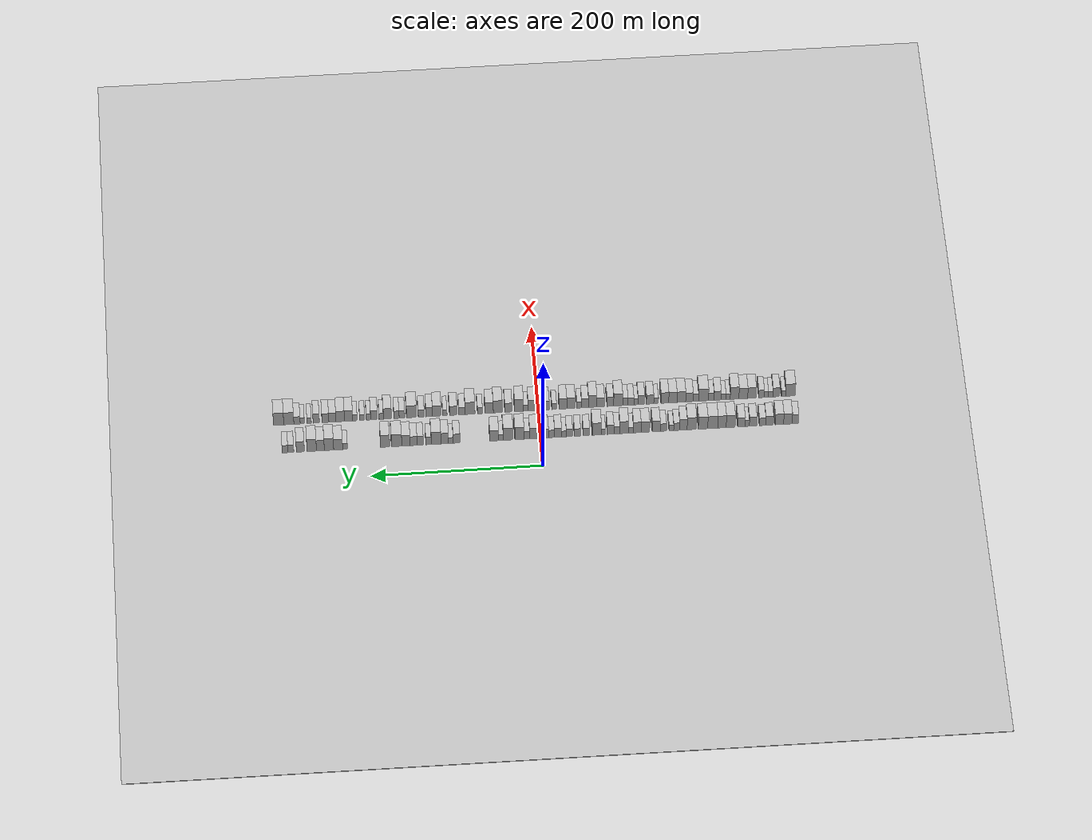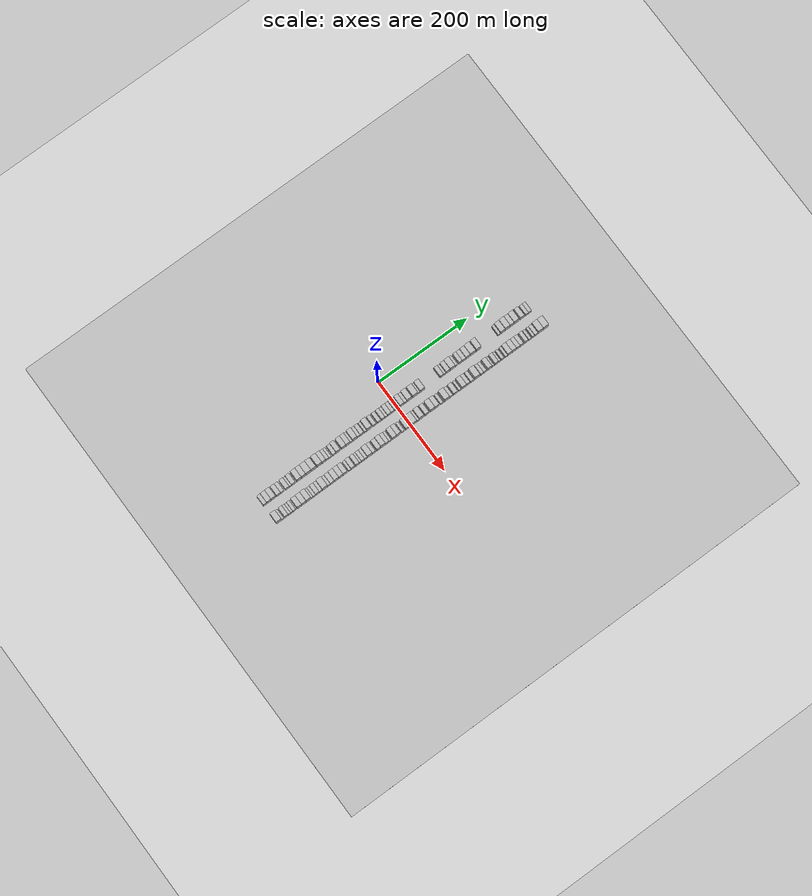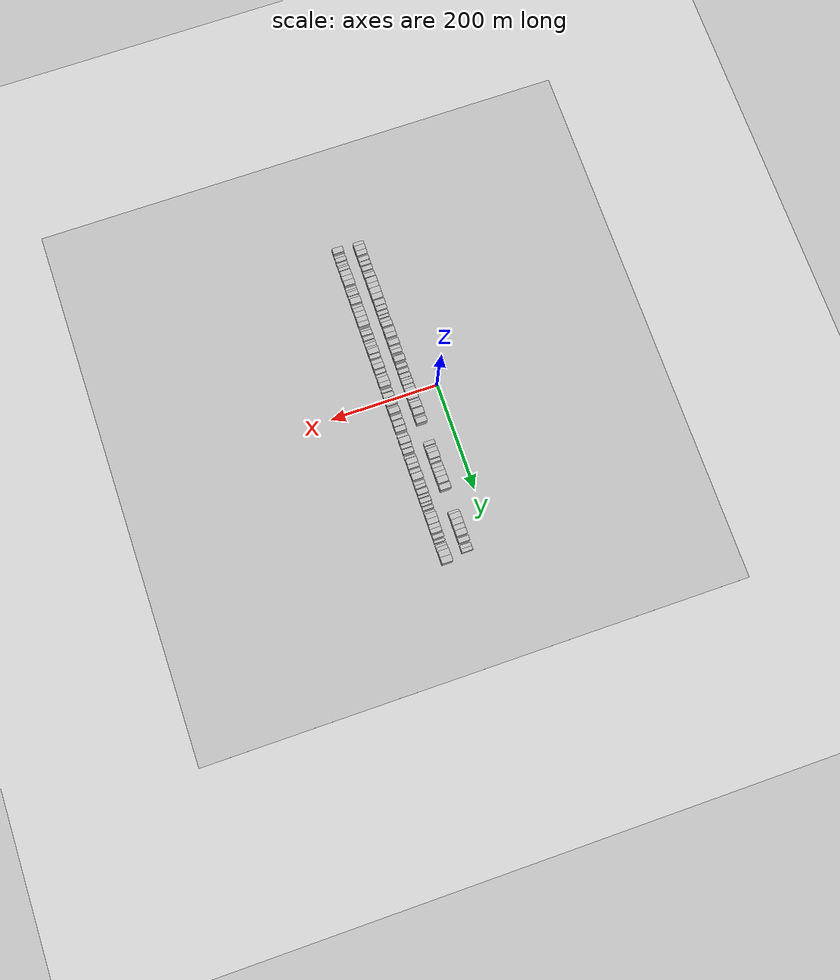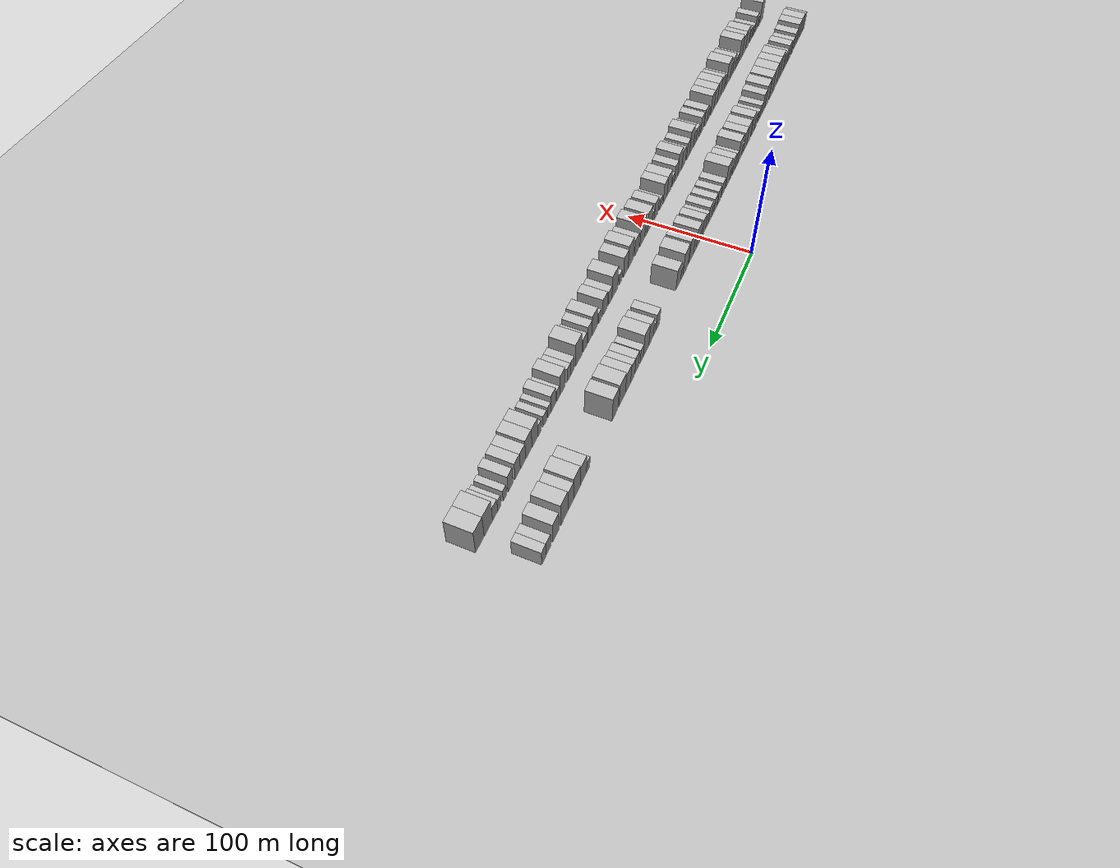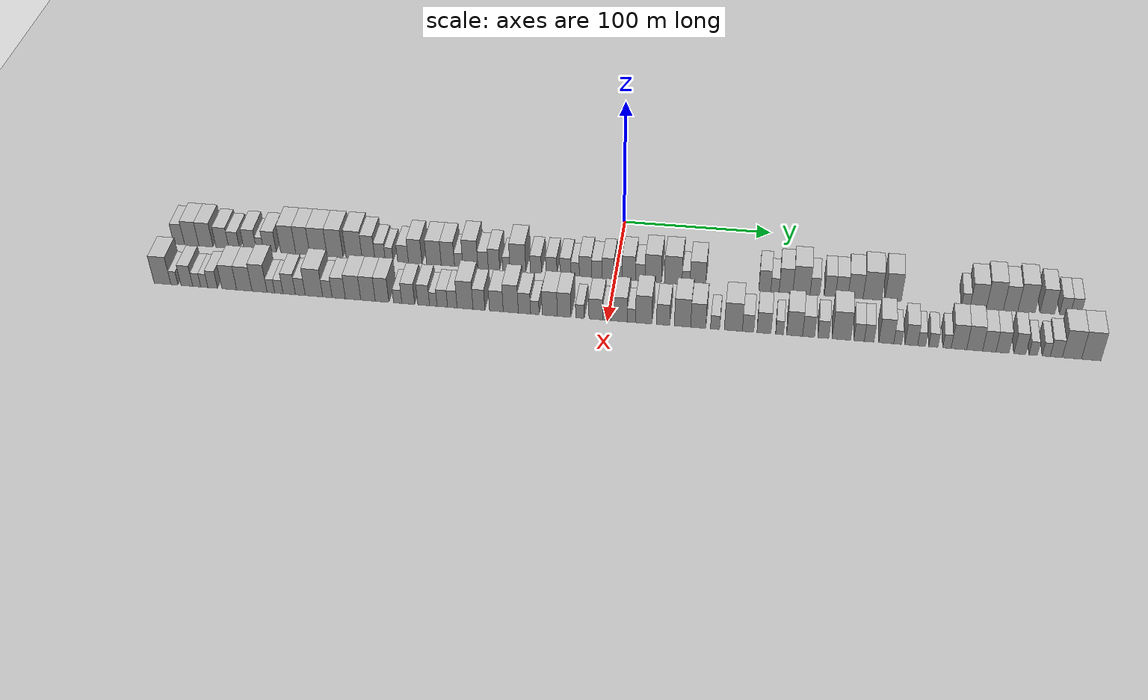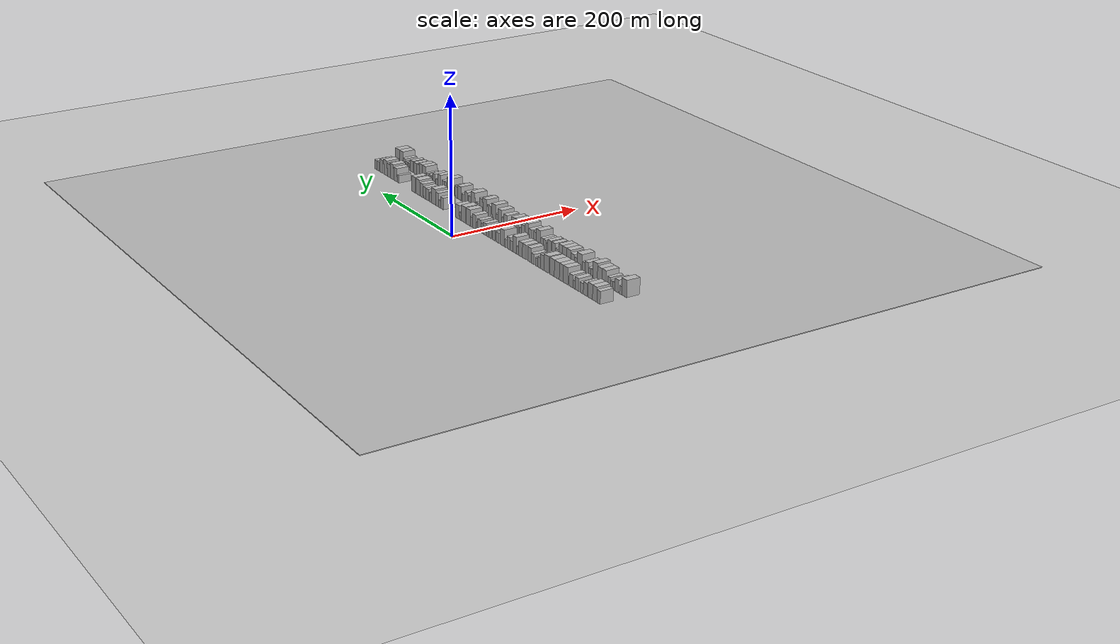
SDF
<?xml version="1.0" encoding="utf-8"?>

<sdf version="1.6">

   <world name="default">

      <gui fullscreen="0">

         <camera name="user_camera">

            <pose>-15 0 4.57585 0 0 0</pose>

            <view_controller>orbit</view_controller>

         </camera>

      </gui>

      <scene>

         <sky>

           <clouds>

             <speed>12</speed>

           </clouds>

         </sky>

         <ambient>0.4 0.4 0.4 1</ambient>

         <background>0.7 0.7 0.7 1</background>

         <shadows>1</shadows>

      </scene>

      <gravity>0 0 -9.8066</gravity>

      <magnetic_field>6e-06 2.3e-05 -4.2e-05</magnetic_field>

      <physics default="0" name="default_physics" type="ode">

         <ode>

            <solver>

               <type>quick</type>

               <iters>10</iters>

               <sor>1.0</sor>

               <use_dynamic_moi_rescaling>0</use_dynamic_moi_rescaling>

            </solver>

            <constraints>

               <cfm>0</cfm>

               <erp>0.2</erp>

               <contact_max_correcting_vel>100</contact_max_correcting_vel>

               <contact_surface_layer>0.001</contact_surface_layer>

            </constraints>

         </ode>

         <max_step_size>0.004</max_step_size>

         <real_time_factor>1</real_time_factor>

         <real_time_update_rate>250</real_time_update_rate>

      </physics>

      <light name="sun" type="directional">

         <cast_shadows>1</cast_shadows>

         <pose>0 0 10 0 0 0</pose>

         <diffuse>0.8 0.8 0.8 1</diffuse>

         <specular>0.2 0.2 0.2 1</specular>

         <attenuation>

            <range>1000</range>

            <constant>0.9</constant>

            <linear>0.01</linear>

            <quadratic>0.001</quadratic>

         </attenuation>

         <direction>-0.5 0.1 -0.9</direction>

      </light>

      <include>

         <name>ground_plane_1</name>

         <uri>model://HANNAS_ground_plane</uri>

         <pose>0 0 0  0 0 0</pose>

      </include>

      <include>

         <name>ground_plane_2</name>

         <uri>model://HANNAS_ground_plane</uri>

         <pose>100 0 0  0 0 0</pose>

      </include>

      <model name="building_1">

         <static>1</static>

         <pose frame="">50.0000 -296.2681 0 0.000000 0.000000 0.000000</pose>

         <link name="link">

            <pose frame="">0 0 9.00 0 0 0</pose>

            <collision name="collision">

               <geometry>

                  <box>

                     <size>20.0000 7.4637 18.0000</size>

                  </box>

               </geometry>

               <max_contacts>10</max_contacts>

               <surface>

                  <contact>

                     <ode/>

                  </contact>

                  <bounce/>

                  <friction>

                     <torsional>

                        <ode/>

                     </torsional>

                     <ode/>

                  </friction>

               </surface>

            </collision>

            <visual name="visual">

               <cast_shadows>0</cast_shadows>

               <geometry>

                  <box>

                     <size>20.0000 7.4637 18.0000</size>

                  </box>

               </geometry>

               <material>

                  <script>

                     <uri>model://HANNAS_wall/materials/scripts</uri>

                     <uri>model://HANNAS_wall/materials/textures</uri>

                     <name>vrc/HANNAS_wall</name>

                  </script>

               </material>

            </visual>

            <self_collide>0</self_collide>

            <enable_wind>0</enable_wind>

            <kinematic>0</kinematic>

         </link>

      </model>

      <model name="building_2">

         <static>1</static>

         <pose frame="">50.0000 -287.5486 0 0.000000 0.000000 0.000000</pose>

         <link name="link">

            <pose frame="">0 0 10.50 0 0 0</pose>

            <collision name="collision">

               <geometry>

                  <box>

                     <size>20.0000 9.9753 21.0000</size>

                  </box>

               </geometry>

               <max_contacts>10</max_contacts>

               <surface>

                  <contact>

                     <ode/>

                  </contact>

                  <bounce/>

                  <friction>

                     <torsional>

                        <ode/>

                     </torsional>

                     <ode/>

                  </friction>

               </surface>

            </collision>

            <visual name="visual">

               <cast_shadows>0</cast_shadows>

               <geometry>

                  <box>

                     <size>20.0000 9.9753 21.0000</size>

                  </box>

               </geometry>

               <material>

                  <script>

                     <uri>model://HANNAS_wall/materials/scripts</uri>

                     <uri>model://HANNAS_wall/materials/textures</uri>

                     <name>vrc/HANNAS_wall</name>

                  </script>

               </material>

            </visual>

            <self_collide>0</self_collide>

            <enable_wind>0</enable_wind>

            <kinematic>0</kinematic>

         </link>

      </model>

      <model name="building_3">

         <static>1</static>

         <pose frame="">50.0000 -277.6109 0 0.000000 0.000000 0.000000</pose>

         <link name="link">

            <pose frame="">0 0 10.50 0 0 0</pose>

            <collision name="collision">

               <geometry>

                  <box>

                     <size>20.0000 9.9003 21.0000</size>

                  </box>

               </geometry>

               <max_contacts>10</max_contacts>

               <surface>

                  <contact>

                     <ode/>

                  </contact>

                  <bounce/>

                  <friction>

                     <torsional>

                        <ode/>

                     </torsional>

                     <ode/>

                  </friction>

               </surface>

            </collision>

            <visual name="visual">

               <cast_shadows>0</cast_shadows>

               <geometry>

                  <box>

                     <size>20.0000 9.9003 21.0000</size>

                  </box>

               </geometry>

               <material>

                  <script>

                     <uri>model://HANNAS_wall/materials/scripts</uri>

                     <uri>model://HANNAS_wall/materials/textures</uri>

                     <name>vrc/HANNAS_wall</name>

                  </script>

               </material>

            </visual>

            <self_collide>0</self_collide>

            <enable_wind>0</enable_wind>

            <kinematic>0</kinematic>

         </link>

      </model>

      <model name="building_4">

         <static>1</static>

         <pose frame="">50.0000 -266.2000 0 0.000000 0.000000 0.000000</pose>

         <link name="link">

            <pose frame="">0 0 9.00 0 0 0</pose>

            <collision name="collision">

               <geometry>

                  <box>

                     <size>20.0000 8.9215 18.0000</size>

                  </box>

               </geometry>

               <max_contacts>10</max_contacts>

               <surface>

                  <contact>

                     <ode/>

                  </contact>

                  <bounce/>

                  <friction>

                     <torsional>

                        <ode/>

                     </torsional>

                     <ode/>

                  </friction>

               </surface>

            </collision>

            <visual name="visual">

               <cast_shadows>0</cast_shadows>

               <geometry>

                  <box>

                     <size>20.0000 8.9215 18.0000</size>

                  </box>

               </geometry>

               <material>

                  <script>

                     <uri>model://HANNAS_wall/materials/scripts</uri>

                     <uri>model://HANNAS_wall/materials/textures</uri>

                     <name>vrc/HANNAS_wall</name>

                  </script>

               </material>

            </visual>

            <self_collide>0</self_collide>

            <enable_wind>0</enable_wind>

            <kinematic>0</kinematic>

         </link>

      </model>

      <model name="building_5">

         <static>1</static>

         <pose frame="">50.0000 -258.0020 0 0.000000 0.000000 0.000000</pose>

         <link name="link">

            <pose frame="">0 0 7.50 0 0 0</pose>

            <collision name="collision">

               <geometry>

                  <box>

                     <size>20.0000 7.4744 15.0000</size>

                  </box>

               </geometry>

               <max_contacts>10</max_contacts>

               <surface>

                  <contact>

                     <ode/>

                  </contact>

                  <bounce/>

                  <friction>

                     <torsional>

                        <ode/>

                     </torsional>

                     <ode/>

                  </friction>

               </surface>

            </collision>

            <visual name="visual">

               <cast_shadows>0</cast_shadows>

               <geometry>

                  <box>

                     <size>20.0000 7.4744 15.0000</size>

                  </box>

               </geometry>

               <material>

                  <script>

                     <uri>model://HANNAS_wall/materials/scripts</uri>

                     <uri>model://HANNAS_wall/materials/textures</uri>

                     <name>vrc/HANNAS_wall</name>

                  </script>

               </material>

            </visual>

            <self_collide>0</self_collide>

            <enable_wind>0</enable_wind>

            <kinematic>0</kinematic>

         </link>

      </model>

      <model name="building_6">

         <static>1</static>

         <pose frame="">50.0000 -246.9356 0 0.000000 0.000000 0.000000</pose>

         <link name="link">

            <pose frame="">0 0 9.00 0 0 0</pose>

            <collision name="collision">

               <geometry>

                  <box>

                     <size>20.0000 8.6585 18.0000</size>

                  </box>

               </geometry>

               <max_contacts>10</max_contacts>

               <surface>

                  <contact>

                     <ode/>

                  </contact>

                  <bounce/>

                  <friction>

                     <torsional>

                        <ode/>

                     </torsional>

                     <ode/>

                  </friction>

               </surface>

            </collision>

            <visual name="visual">

               <cast_shadows>0</cast_shadows>

               <geometry>

                  <box>

                     <size>20.0000 8.6585 18.0000</size>

                  </box>

               </geometry>

               <material>

                  <script>

                     <uri>model://HANNAS_wall/materials/scripts</uri>

                     <uri>model://HANNAS_wall/materials/textures</uri>

                     <name>vrc/HANNAS_wall</name>

                  </script>

               </material>

            </visual>

            <self_collide>0</self_collide>

            <enable_wind>0</enable_wind>

            <kinematic>0</kinematic>

         </link>

      </model>

      <model name="building_7">

         <static>1</static>

         <pose frame="">50.0000 -240.1300 0 0.000000 0.000000 0.000000</pose>

         <link name="link">

            <pose frame="">0 0 6.00 0 0 0</pose>

            <collision name="collision">

               <geometry>

                  <box>

                     <size>20.0000 4.9528 12.0000</size>

                  </box>

               </geometry>

               <max_contacts>10</max_contacts>

               <surface>

                  <contact>

                     <ode/>

                  </contact>

                  <bounce/>

                  <friction>

                     <torsional>

                        <ode/>

                     </torsional>

                     <ode/>

                  </friction>

               </surface>

            </collision>

            <visual name="visual">

               <cast_shadows>0</cast_shadows>

               <geometry>

                  <box>

                     <size>20.0000 4.9528 12.0000</size>

                  </box>

               </geometry>

               <material>

                  <script>

                     <uri>model://HANNAS_wall/materials/scripts</uri>

                     <uri>model://HANNAS_wall/materials/textures</uri>

                     <name>vrc/HANNAS_wall</name>

                  </script>

               </material>

            </visual>

            <self_collide>0</self_collide>

            <enable_wind>0</enable_wind>

            <kinematic>0</kinematic>

         </link>

      </model>

      <model name="building_8">

         <static>1</static>

         <pose frame="">50.0000 -233.3050 0 0.000000 0.000000 0.000000</pose>

         <link name="link">

            <pose frame="">0 0 9.00 0 0 0</pose>

            <collision name="collision">

               <geometry>

                  <box>

                     <size>20.0000 8.6971 18.0000</size>

                  </box>

               </geometry>

               <max_contacts>10</max_contacts>

               <surface>

                  <contact>

                     <ode/>

                  </contact>

                  <bounce/>

                  <friction>

                     <torsional>

                        <ode/>

                     </torsional>

                     <ode/>

                  </friction>

               </surface>

            </collision>

            <visual name="visual">

               <cast_shadows>0</cast_shadows>

               <geometry>

                  <box>

                     <size>20.0000 8.6971 18.0000</size>

                  </box>

               </geometry>

               <material>

                  <script>

                     <uri>model://HANNAS_wall/materials/scripts</uri>

                     <uri>model://HANNAS_wall/materials/textures</uri>

                     <name>vrc/HANNAS_wall</name>

                  </script>

               </material>

            </visual>

            <self_collide>0</self_collide>

            <enable_wind>0</enable_wind>

            <kinematic>0</kinematic>

         </link>

      </model>

      <model name="building_9">

         <static>1</static>

         <pose frame="">50.0000 -220.7380 0 0.000000 0.000000 0.000000</pose>

         <link name="link">

            <pose frame="">0 0 12.00 0 0 0</pose>

            <collision name="collision">

               <geometry>

                  <box>

                     <size>20.0000 10.4370 24.0000</size>

                  </box>

               </geometry>

               <max_contacts>10</max_contacts>

               <surface>

                  <contact>

                     <ode/>

                  </contact>

                  <bounce/>

                  <friction>

                     <torsional>

                        <ode/>

                     </torsional>

                     <ode/>

                  </friction>

               </surface>

            </collision>

            <visual name="visual">

               <cast_shadows>0</cast_shadows>

               <geometry>

                  <box>

                     <size>20.0000 10.4370 24.0000</size>

                  </box>

               </geometry>

               <material>

                  <script>

                     <uri>model://HANNAS_wall/materials/scripts</uri>

                     <uri>model://HANNAS_wall/materials/textures</uri>

                     <name>vrc/HANNAS_wall</name>

                  </script>

               </material>

            </visual>

            <self_collide>0</self_collide>

            <enable_wind>0</enable_wind>

            <kinematic>0</kinematic>

         </link>

      </model>

      <model name="building_10">

         <static>1</static>

         <pose frame="">50.0000 -210.6921 0 0.000000 0.000000 0.000000</pose>

         <link name="link">

            <pose frame="">0 0 12.00 0 0 0</pose>

            <collision name="collision">

               <geometry>

                  <box>

                     <size>20.0000 9.6547 24.0000</size>

                  </box>

               </geometry>

               <max_contacts>10</max_contacts>

               <surface>

                  <contact>

                     <ode/>

                  </contact>

                  <bounce/>

                  <friction>

                     <torsional>

                        <ode/>

                     </torsional>

                     <ode/>

                  </friction>

               </surface>

            </collision>

            <visual name="visual">

               <cast_shadows>0</cast_shadows>

               <geometry>

                  <box>

                     <size>20.0000 9.6547 24.0000</size>

                  </box>

               </geometry>

               <material>

                  <script>

                     <uri>model://HANNAS_wall/materials/scripts</uri>

                     <uri>model://HANNAS_wall/materials/textures</uri>

                     <name>vrc/HANNAS_wall</name>

                  </script>

               </material>

            </visual>

            <self_collide>0</self_collide>

            <enable_wind>0</enable_wind>

            <kinematic>0</kinematic>

         </link>

      </model>

      <model name="building_11">

         <static>1</static>

         <pose frame="">50.0000 -199.9484 0 0.000000 0.000000 0.000000</pose>

         <link name="link">

            <pose frame="">0 0 12.00 0 0 0</pose>

            <collision name="collision">

               <geometry>

                  <box>

                     <size>20.0000 11.8328 24.0000</size>

                  </box>

               </geometry>

               <max_contacts>10</max_contacts>

               <surface>

                  <contact>

                     <ode/>

                  </contact>

                  <bounce/>

                  <friction>

                     <torsional>

                        <ode/>

                     </torsional>

                     <ode/>

                  </friction>

               </surface>

            </collision>

            <visual name="visual">

               <cast_shadows>0</cast_shadows>

               <geometry>

                  <box>

                     <size>20.0000 11.8328 24.0000</size>

                  </box>

               </geometry>

               <material>

                  <script>

                     <uri>model://HANNAS_wall/materials/scripts</uri>

                     <uri>model://HANNAS_wall/materials/textures</uri>

                     <name>vrc/HANNAS_wall</name>

                  </script>

               </material>

            </visual>

            <self_collide>0</self_collide>

            <enable_wind>0</enable_wind>

            <kinematic>0</kinematic>

         </link>

      </model>

      <model name="building_12">

         <static>1</static>

         <pose frame="">50.0000 -188.5231 0 0.000000 0.000000 0.000000</pose>

         <link name="link">

            <pose frame="">0 0 12.00 0 0 0</pose>

            <collision name="collision">

               <geometry>

                  <box>

                     <size>20.0000 11.0177 24.0000</size>

                  </box>

               </geometry>

               <max_contacts>10</max_contacts>

               <surface>

                  <contact>

                     <ode/>

                  </contact>

                  <bounce/>

                  <friction>

                     <torsional>

                        <ode/>

                     </torsional>

                     <ode/>

                  </friction>

               </surface>

            </collision>

            <visual name="visual">

               <cast_shadows>0</cast_shadows>

               <geometry>

                  <box>

                     <size>20.0000 11.0177 24.0000</size>

                  </box>

               </geometry>

               <material>

                  <script>

                     <uri>model://HANNAS_wall/materials/scripts</uri>

                     <uri>model://HANNAS_wall/materials/textures</uri>

                     <name>vrc/HANNAS_wall</name>

                  </script>

               </material>

            </visual>

            <self_collide>0</self_collide>

            <enable_wind>0</enable_wind>

            <kinematic>0</kinematic>

         </link>

      </model>

      <model name="building_13">

         <static>1</static>

         <pose frame="">50.0000 -175.4865 0 0.000000 0.000000 0.000000</pose>

         <link name="link">

            <pose frame="">0 0 12.00 0 0 0</pose>

            <collision name="collision">

               <geometry>

                  <box>

                     <size>20.0000 11.0557 24.0000</size>

                  </box>

               </geometry>

               <max_contacts>10</max_contacts>

               <surface>

                  <contact>

                     <ode/>

                  </contact>

                  <bounce/>

                  <friction>

                     <torsional>

                        <ode/>

                     </torsional>

                     <ode/>

                  </friction>

               </surface>

            </collision>

            <visual name="visual">

               <cast_shadows>0</cast_shadows>

               <geometry>

                  <box>

                     <size>20.0000 11.0557 24.0000</size>

                  </box>

               </geometry>

               <material>

                  <script>

                     <uri>model://HANNAS_wall/materials/scripts</uri>

                     <uri>model://HANNAS_wall/materials/textures</uri>

                     <name>vrc/HANNAS_wall</name>

                  </script>

               </material>

            </visual>

            <self_collide>0</self_collide>

            <enable_wind>0</enable_wind>

            <kinematic>0</kinematic>

         </link>

      </model>

      <model name="building_14">

         <static>1</static>

         <pose frame="">50.0000 -165.6355 0 0.000000 0.000000 0.000000</pose>

         <link name="link">

            <pose frame="">0 0 10.50 0 0 0</pose>

            <collision name="collision">

               <geometry>

                  <box>

                     <size>20.0000 8.6461 21.0000</size>

                  </box>

               </geometry>

               <max_contacts>10</max_contacts>

               <surface>

                  <contact>

                     <ode/>

                  </contact>

                  <bounce/>

                  <friction>

                     <torsional>

                        <ode/>

                     </torsional>

                     <ode/>

                  </friction>

               </surface>

            </collision>

            <visual name="visual">

               <cast_shadows>0</cast_shadows>

               <geometry>

                  <box>

                     <size>20.0000 8.6461 21.0000</size>

                  </box>

               </geometry>

               <material>

                  <script>

                     <uri>model://HANNAS_wall/materials/scripts</uri>

                     <uri>model://HANNAS_wall/materials/textures</uri>

                     <name>vrc/HANNAS_wall</name>

                  </script>

               </material>

            </visual>

            <self_collide>0</self_collide>

            <enable_wind>0</enable_wind>

            <kinematic>0</kinematic>

         </link>

      </model>

      <model name="building_15">

         <static>1</static>

         <pose frame="">50.0000 -157.7900 0 0.000000 0.000000 0.000000</pose>

         <link name="link">

            <pose frame="">0 0 7.50 0 0 0</pose>

            <collision name="collision">

               <geometry>

                  <box>

                     <size>20.0000 7.0449 15.0000</size>

                  </box>

               </geometry>

               <max_contacts>10</max_contacts>

               <surface>

                  <contact>

                     <ode/>

                  </contact>

                  <bounce/>

                  <friction>

                     <torsional>

                        <ode/>

                     </torsional>

                     <ode/>

                  </friction>

               </surface>

            </collision>

            <visual name="visual">

               <cast_shadows>0</cast_shadows>

               <geometry>

                  <box>

                     <size>20.0000 7.0449 15.0000</size>

                  </box>

               </geometry>

               <material>

                  <script>

                     <uri>model://HANNAS_wall/materials/scripts</uri>

                     <uri>model://HANNAS_wall/materials/textures</uri>

                     <name>vrc/HANNAS_wall</name>

                  </script>

               </material>

            </visual>

            <self_collide>0</self_collide>

            <enable_wind>0</enable_wind>

            <kinematic>0</kinematic>

         </link>

      </model>

      <model name="building_16">

         <static>1</static>

         <pose frame="">50.0000 -151.5792 0 0.000000 0.000000 0.000000</pose>

         <link name="link">

            <pose frame="">0 0 6.00 0 0 0</pose>

            <collision name="collision">

               <geometry>

                  <box>

                     <size>20.0000 5.3768 12.0000</size>

                  </box>

               </geometry>

               <max_contacts>10</max_contacts>

               <surface>

                  <contact>

                     <ode/>

                  </contact>

                  <bounce/>

                  <friction>

                     <torsional>

                        <ode/>

                     </torsional>

                     <ode/>

                  </friction>

               </surface>

            </collision>

            <visual name="visual">

               <cast_shadows>0</cast_shadows>

               <geometry>

                  <box>

                     <size>20.0000 5.3768 12.0000</size>

                  </box>

               </geometry>

               <material>

                  <script>

                     <uri>model://HANNAS_wall/materials/scripts</uri>

                     <uri>model://HANNAS_wall/materials/textures</uri>

                     <name>vrc/HANNAS_wall</name>

                  </script>

               </material>

            </visual>

            <self_collide>0</self_collide>

            <enable_wind>0</enable_wind>

            <kinematic>0</kinematic>

         </link>

      </model>

      <model name="building_17">

         <static>1</static>

         <pose frame="">50.0000 -142.1929 0 0.000000 0.000000 0.000000</pose>

         <link name="link">

            <pose frame="">0 0 7.50 0 0 0</pose>

            <collision name="collision">

               <geometry>

                  <box>

                     <size>20.0000 7.3958 15.0000</size>

                  </box>

               </geometry>

               <max_contacts>10</max_contacts>

               <surface>

                  <contact>

                     <ode/>

                  </contact>

                  <bounce/>

                  <friction>

                     <torsional>

                        <ode/>

                     </torsional>

                     <ode/>

                  </friction>

               </surface>

            </collision>

            <visual name="visual">

               <cast_shadows>0</cast_shadows>

               <geometry>

                  <box>

                     <size>20.0000 7.3958 15.0000</size>

                  </box>

               </geometry>

               <material>

                  <script>

                     <uri>model://HANNAS_wall/materials/scripts</uri>

                     <uri>model://HANNAS_wall/materials/textures</uri>

                     <name>vrc/HANNAS_wall</name>

                  </script>

               </material>

            </visual>

            <self_collide>0</self_collide>

            <enable_wind>0</enable_wind>

            <kinematic>0</kinematic>

         </link>

      </model>

      <model name="building_18">

         <static>1</static>

         <pose frame="">50.0000 -133.8683 0 0.000000 0.000000 0.000000</pose>

         <link name="link">

            <pose frame="">0 0 10.50 0 0 0</pose>

            <collision name="collision">

               <geometry>

                  <box>

                     <size>20.0000 9.2536 21.0000</size>

                  </box>

               </geometry>

               <max_contacts>10</max_contacts>

               <surface>

                  <contact>

                     <ode/>

                  </contact>

                  <bounce/>

                  <friction>

                     <torsional>

                        <ode/>

                     </torsional>

                     <ode/>

                  </friction>

               </surface>

            </collision>

            <visual name="visual">

               <cast_shadows>0</cast_shadows>

               <geometry>

                  <box>

                     <size>20.0000 9.2536 21.0000</size>

                  </box>

               </geometry>

               <material>

                  <script>

                     <uri>model://HANNAS_wall/materials/scripts</uri>

                     <uri>model://HANNAS_wall/materials/textures</uri>

                     <name>vrc/HANNAS_wall</name>

                  </script>

               </material>

            </visual>

            <self_collide>0</self_collide>

            <enable_wind>0</enable_wind>

            <kinematic>0</kinematic>

         </link>

      </model>

      <model name="building_19">

         <static>1</static>

         <pose frame="">50.0000 -121.2413 0 0.000000 0.000000 0.000000</pose>

         <link name="link">

            <pose frame="">0 0 10.50 0 0 0</pose>

            <collision name="collision">

               <geometry>

                  <box>

                     <size>20.0000 10.0004 21.0000</size>

                  </box>

               </geometry>

               <max_contacts>10</max_contacts>

               <surface>

                  <contact>

                     <ode/>

                  </contact>

                  <bounce/>

                  <friction>

                     <torsional>

                        <ode/>

                     </torsional>

                     <ode/>

                  </friction>

               </surface>

            </collision>

            <visual name="visual">

               <cast_shadows>0</cast_shadows>

               <geometry>

                  <box>

                     <size>20.0000 10.0004 21.0000</size>

                  </box>

               </geometry>

               <material>

                  <script>

                     <uri>model://HANNAS_wall/materials/scripts</uri>

                     <uri>model://HANNAS_wall/materials/textures</uri>

                     <name>vrc/HANNAS_wall</name>

                  </script>

               </material>

            </visual>

            <self_collide>0</self_collide>

            <enable_wind>0</enable_wind>

            <kinematic>0</kinematic>

         </link>

      </model>

      <model name="building_20">

         <static>1</static>

         <pose frame="">50.0000 -111.7698 0 0.000000 0.000000 0.000000</pose>

         <link name="link">

            <pose frame="">0 0 10.50 0 0 0</pose>

            <collision name="collision">

               <geometry>

                  <box>

                     <size>20.0000 8.9425 21.0000</size>

                  </box>

               </geometry>

               <max_contacts>10</max_contacts>

               <surface>

                  <contact>

                     <ode/>

                  </contact>

                  <bounce/>

                  <friction>

                     <torsional>

                        <ode/>

                     </torsional>

                     <ode/>

                  </friction>

               </surface>

            </collision>

            <visual name="visual">

               <cast_shadows>0</cast_shadows>

               <geometry>

                  <box>

                     <size>20.0000 8.9425 21.0000</size>

                  </box>

               </geometry>

               <material>

                  <script>

                     <uri>model://HANNAS_wall/materials/scripts</uri>

                     <uri>model://HANNAS_wall/materials/textures</uri>

                     <name>vrc/HANNAS_wall</name>

                  </script>

               </material>

            </visual>

            <self_collide>0</self_collide>

            <enable_wind>0</enable_wind>

            <kinematic>0</kinematic>

         </link>

      </model>

      <model name="building_21">

         <static>1</static>

         <pose frame="">50.0000 -104.4695 0 0.000000 0.000000 0.000000</pose>

         <link name="link">

            <pose frame="">0 0 6.00 0 0 0</pose>

            <collision name="collision">

               <geometry>

                  <box>

                     <size>20.0000 5.6582 12.0000</size>

                  </box>

               </geometry>

               <max_contacts>10</max_contacts>

               <surface>

                  <contact>

                     <ode/>

                  </contact>

                  <bounce/>

                  <friction>

                     <torsional>

                        <ode/>

                     </torsional>

                     <ode/>

                  </friction>

               </surface>

            </collision>

            <visual name="visual">

               <cast_shadows>0</cast_shadows>

               <geometry>

                  <box>

                     <size>20.0000 5.6582 12.0000</size>

                  </box>

               </geometry>

               <material>

                  <script>

                     <uri>model://HANNAS_wall/materials/scripts</uri>

                     <uri>model://HANNAS_wall/materials/textures</uri>

                     <name>vrc/HANNAS_wall</name>

                  </script>

               </material>

            </visual>

            <self_collide>0</self_collide>

            <enable_wind>0</enable_wind>

            <kinematic>0</kinematic>

         </link>

      </model>

      <model name="building_22">

         <static>1</static>

         <pose frame="">50.0000 -96.5755 0 0.000000 0.000000 0.000000</pose>

         <link name="link">

            <pose frame="">0 0 12.00 0 0 0</pose>

            <collision name="collision">

               <geometry>

                  <box>

                     <size>20.0000 10.1298 24.0000</size>

                  </box>

               </geometry>

               <max_contacts>10</max_contacts>

               <surface>

                  <contact>

                     <ode/>

                  </contact>

                  <bounce/>

                  <friction>

                     <torsional>

                        <ode/>

                     </torsional>

                     <ode/>

                  </friction>

               </surface>

            </collision>

            <visual name="visual">

               <cast_shadows>0</cast_shadows>

               <geometry>

                  <box>

                     <size>20.0000 10.1298 24.0000</size>

                  </box>

               </geometry>

               <material>

                  <script>

                     <uri>model://HANNAS_wall/materials/scripts</uri>

                     <uri>model://HANNAS_wall/materials/textures</uri>

                     <name>vrc/HANNAS_wall</name>

                  </script>

               </material>

            </visual>

            <self_collide>0</self_collide>

            <enable_wind>0</enable_wind>

            <kinematic>0</kinematic>

         </link>

      </model>

      <model name="building_23">

         <static>1</static>

         <pose frame="">50.0000 -88.0419 0 0.000000 0.000000 0.000000</pose>

         <link name="link">

            <pose frame="">0 0 7.50 0 0 0</pose>

            <collision name="collision">

               <geometry>

                  <box>

                     <size>20.0000 6.9375 15.0000</size>

                  </box>

               </geometry>

               <max_contacts>10</max_contacts>

               <surface>

                  <contact>

                     <ode/>

                  </contact>

                  <bounce/>

                  <friction>

                     <torsional>

                        <ode/>

                     </torsional>

                     <ode/>

                  </friction>

               </surface>

            </collision>

            <visual name="visual">

               <cast_shadows>0</cast_shadows>

               <geometry>

                  <box>

                     <size>20.0000 6.9375 15.0000</size>

                  </box>

               </geometry>

               <material>

                  <script>

                     <uri>model://HANNAS_wall/materials/scripts</uri>

                     <uri>model://HANNAS_wall/materials/textures</uri>

                     <name>vrc/HANNAS_wall</name>

                  </script>

               </material>

            </visual>

            <self_collide>0</self_collide>

            <enable_wind>0</enable_wind>

            <kinematic>0</kinematic>

         </link>

      </model>

      <model name="building_24">

         <static>1</static>

         <pose frame="">50.0000 -80.7209 0 0.000000 0.000000 0.000000</pose>

         <link name="link">

            <pose frame="">0 0 9.00 0 0 0</pose>

            <collision name="collision">

               <geometry>

                  <box>

                     <size>20.0000 7.7043 18.0000</size>

                  </box>

               </geometry>

               <max_contacts>10</max_contacts>

               <surface>

                  <contact>

                     <ode/>

                  </contact>

                  <bounce/>

                  <friction>

                     <torsional>

                        <ode/>

                     </torsional>

                     <ode/>

                  </friction>

               </surface>

            </collision>

            <visual name="visual">

               <cast_shadows>0</cast_shadows>

               <geometry>

                  <box>

                     <size>20.0000 7.7043 18.0000</size>

                  </box>

               </geometry>

               <material>

                  <script>

                     <uri>model://HANNAS_wall/materials/scripts</uri>

                     <uri>model://HANNAS_wall/materials/textures</uri>

                     <name>vrc/HANNAS_wall</name>

                  </script>

               </material>

            </visual>

            <self_collide>0</self_collide>

            <enable_wind>0</enable_wind>

            <kinematic>0</kinematic>

         </link>

      </model>

      <model name="building_25">

         <static>1</static>

         <pose frame="">50.0000 -72.4172 0 0.000000 0.000000 0.000000</pose>

         <link name="link">

            <pose frame="">0 0 6.00 0 0 0</pose>

            <collision name="collision">

               <geometry>

                  <box>

                     <size>20.0000 4.9032 12.0000</size>

                  </box>

               </geometry>

               <max_contacts>10</max_contacts>

               <surface>

                  <contact>

                     <ode/>

                  </contact>

                  <bounce/>

                  <friction>

                     <torsional>

                        <ode/>

                     </torsional>

                     <ode/>

                  </friction>

               </surface>

            </collision>

            <visual name="visual">

               <cast_shadows>0</cast_shadows>

               <geometry>

                  <box>

                     <size>20.0000 4.9032 12.0000</size>

                  </box>

               </geometry>

               <material>

                  <script>

                     <uri>model://HANNAS_wall/materials/scripts</uri>

                     <uri>model://HANNAS_wall/materials/textures</uri>

                     <name>vrc/HANNAS_wall</name>

                  </script>

               </material>

            </visual>

            <self_collide>0</self_collide>

            <enable_wind>0</enable_wind>

            <kinematic>0</kinematic>

         </link>

      </model>

      <model name="building_26">

         <static>1</static>

         <pose frame="">50.0000 -64.6622 0 0.000000 0.000000 0.000000</pose>

         <link name="link">

            <pose frame="">0 0 12.00 0 0 0</pose>

            <collision name="collision">

               <geometry>

                  <box>

                     <size>20.0000 10.6067 24.0000</size>

                  </box>

               </geometry>

               <max_contacts>10</max_contacts>

               <surface>

                  <contact>

                     <ode/>

                  </contact>

                  <bounce/>

                  <friction>

                     <torsional>

                        <ode/>

                     </torsional>

                     <ode/>

                  </friction>

               </surface>

            </collision>

            <visual name="visual">

               <cast_shadows>0</cast_shadows>

               <geometry>

                  <box>

                     <size>20.0000 10.6067 24.0000</size>

                  </box>

               </geometry>

               <material>

                  <script>

                     <uri>model://HANNAS_wall/materials/scripts</uri>

                     <uri>model://HANNAS_wall/materials/textures</uri>

                     <name>vrc/HANNAS_wall</name>

                  </script>

               </material>

            </visual>

            <self_collide>0</self_collide>

            <enable_wind>0</enable_wind>

            <kinematic>0</kinematic>

         </link>

      </model>

      <model name="building_27">

         <static>1</static>

         <pose frame="">50.0000 -52.6284 0 0.000000 0.000000 0.000000</pose>

         <link name="link">

            <pose frame="">0 0 7.50 0 0 0</pose>

            <collision name="collision">

               <geometry>

                  <box>

                     <size>20.0000 7.4610 15.0000</size>

                  </box>

               </geometry>

               <max_contacts>10</max_contacts>

               <surface>

                  <contact>

                     <ode/>

                  </contact>

                  <bounce/>

                  <friction>

                     <torsional>

                        <ode/>

                     </torsional>

                     <ode/>

                  </friction>

               </surface>

            </collision>

            <visual name="visual">

               <cast_shadows>0</cast_shadows>

               <geometry>

                  <box>

                     <size>20.0000 7.4610 15.0000</size>

                  </box>

               </geometry>

               <material>

                  <script>

                     <uri>model://HANNAS_wall/materials/scripts</uri>

                     <uri>model://HANNAS_wall/materials/textures</uri>

                     <name>vrc/HANNAS_wall</name>

                  </script>

               </material>

            </visual>

            <self_collide>0</self_collide>

            <enable_wind>0</enable_wind>

            <kinematic>0</kinematic>

         </link>

      </model>

      <model name="building_28">

         <static>1</static>

         <pose frame="">50.0000 -42.2140 0 0.000000 0.000000 0.000000</pose>

         <link name="link">

            <pose frame="">0 0 7.50 0 0 0</pose>

            <collision name="collision">

               <geometry>

                  <box>

                     <size>20.0000 7.3677 15.0000</size>

                  </box>

               </geometry>

               <max_contacts>10</max_contacts>

               <surface>

                  <contact>

                     <ode/>

                  </contact>

                  <bounce/>

                  <friction>

                     <torsional>

                        <ode/>

                     </torsional>

                     <ode/>

                  </friction>

               </surface>

            </collision>

            <visual name="visual">

               <cast_shadows>0</cast_shadows>

               <geometry>

                  <box>

                     <size>20.0000 7.3677 15.0000</size>

                  </box>

               </geometry>

               <material>

                  <script>

                     <uri>model://HANNAS_wall/materials/scripts</uri>

                     <uri>model://HANNAS_wall/materials/textures</uri>

                     <name>vrc/HANNAS_wall</name>

                  </script>

               </material>

            </visual>

            <self_collide>0</self_collide>

            <enable_wind>0</enable_wind>

            <kinematic>0</kinematic>

         </link>

      </model>

      <model name="building_29">

         <static>1</static>

         <pose frame="">50.0000 -32.8546 0 0.000000 0.000000 0.000000</pose>

         <link name="link">

            <pose frame="">0 0 7.50 0 0 0</pose>

            <collision name="collision">

               <geometry>

                  <box>

                     <size>20.0000 7.3512 15.0000</size>

                  </box>

               </geometry>

               <max_contacts>10</max_contacts>

               <surface>

                  <contact>

                     <ode/>

                  </contact>

                  <bounce/>

                  <friction>

                     <torsional>

                        <ode/>

                     </torsional>

                     <ode/>

                  </friction>

               </surface>

            </collision>

            <visual name="visual">

               <cast_shadows>0</cast_shadows>

               <geometry>

                  <box>

                     <size>20.0000 7.3512 15.0000</size>

                  </box>

               </geometry>

               <material>

                  <script>

                     <uri>model://HANNAS_wall/materials/scripts</uri>

                     <uri>model://HANNAS_wall/materials/textures</uri>

                     <name>vrc/HANNAS_wall</name>

                  </script>

               </material>

            </visual>

            <self_collide>0</self_collide>

            <enable_wind>0</enable_wind>

            <kinematic>0</kinematic>

         </link>

      </model>

      <model name="building_30">

         <static>1</static>

         <pose frame="">50.0000 -26.4190 0 0.000000 0.000000 0.000000</pose>

         <link name="link">

            <pose frame="">0 0 6.00 0 0 0</pose>

            <collision name="collision">

               <geometry>

                  <box>

                     <size>20.0000 5.5198 12.0000</size>

                  </box>

               </geometry>

               <max_contacts>10</max_contacts>

               <surface>

                  <contact>

                     <ode/>

                  </contact>

                  <bounce/>

                  <friction>

                     <torsional>

                        <ode/>

                     </torsional>

                     <ode/>

                  </friction>

               </surface>

            </collision>

            <visual name="visual">

               <cast_shadows>0</cast_shadows>

               <geometry>

                  <box>

                     <size>20.0000 5.5198 12.0000</size>

                  </box>

               </geometry>

               <material>

                  <script>

                     <uri>model://HANNAS_wall/materials/scripts</uri>

                     <uri>model://HANNAS_wall/materials/textures</uri>

                     <name>vrc/HANNAS_wall</name>

                  </script>

               </material>

            </visual>

            <self_collide>0</self_collide>

            <enable_wind>0</enable_wind>

            <kinematic>0</kinematic>

         </link>

      </model>

      <model name="building_31">

         <static>1</static>

         <pose frame="">50.0000 -19.6068 0 0.000000 0.000000 0.000000</pose>

         <link name="link">

            <pose frame="">0 0 9.00 0 0 0</pose>

            <collision name="collision">

               <geometry>

                  <box>

                     <size>20.0000 8.1047 18.0000</size>

                  </box>

               </geometry>

               <max_contacts>10</max_contacts>

               <surface>

                  <contact>

                     <ode/>

                  </contact>

                  <bounce/>

                  <friction>

                     <torsional>

                        <ode/>

                     </torsional>

                     <ode/>

                  </friction>

               </surface>

            </collision>

            <visual name="visual">

               <cast_shadows>0</cast_shadows>

               <geometry>

                  <box>

                     <size>20.0000 8.1047 18.0000</size>

                  </box>

               </geometry>

               <material>

                  <script>

                     <uri>model://HANNAS_wall/materials/scripts</uri>

                     <uri>model://HANNAS_wall/materials/textures</uri>

                     <name>vrc/HANNAS_wall</name>

                  </script>

               </material>

            </visual>

            <self_collide>0</self_collide>

            <enable_wind>0</enable_wind>

            <kinematic>0</kinematic>

         </link>

      </model>

      <model name="building_32">

         <static>1</static>

         <pose frame="">50.0000 -12.0020 0 0.000000 0.000000 0.000000</pose>

         <link name="link">

            <pose frame="">0 0 7.50 0 0 0</pose>

            <collision name="collision">

               <geometry>

                  <box>

                     <size>20.0000 7.1049 15.0000</size>

                  </box>

               </geometry>

               <max_contacts>10</max_contacts>

               <surface>

                  <contact>

                     <ode/>

                  </contact>

                  <bounce/>

                  <friction>

                     <torsional>

                        <ode/>

                     </torsional>

                     <ode/>

                  </friction>

               </surface>

            </collision>

            <visual name="visual">

               <cast_shadows>0</cast_shadows>

               <geometry>

                  <box>

                     <size>20.0000 7.1049 15.0000</size>

                  </box>

               </geometry>

               <material>

                  <script>

                     <uri>model://HANNAS_wall/materials/scripts</uri>

                     <uri>model://HANNAS_wall/materials/textures</uri>

                     <name>vrc/HANNAS_wall</name>

                  </script>

               </material>

            </visual>

            <self_collide>0</self_collide>

            <enable_wind>0</enable_wind>

            <kinematic>0</kinematic>

         </link>

      </model>

      <model name="building_33">

         <static>1</static>

         <pose frame="">50.0000 -4.5010 0 0.000000 0.000000 0.000000</pose>

         <link name="link">

            <pose frame="">0 0 9.00 0 0 0</pose>

            <collision name="collision">

               <geometry>

                  <box>

                     <size>20.0000 7.8972 18.0000</size>

                  </box>

               </geometry>

               <max_contacts>10</max_contacts>

               <surface>

                  <contact>

                     <ode/>

                  </contact>

                  <bounce/>

                  <friction>

                     <torsional>

                        <ode/>

                     </torsional>

                     <ode/>

                  </friction>

               </surface>

            </collision>

            <visual name="visual">

               <cast_shadows>0</cast_shadows>

               <geometry>

                  <box>

                     <size>20.0000 7.8972 18.0000</size>

                  </box>

               </geometry>

               <material>

                  <script>

                     <uri>model://HANNAS_wall/materials/scripts</uri>

                     <uri>model://HANNAS_wall/materials/textures</uri>

                     <name>vrc/HANNAS_wall</name>

                  </script>

               </material>

            </visual>

            <self_collide>0</self_collide>

            <enable_wind>0</enable_wind>

            <kinematic>0</kinematic>

         </link>

      </model>

      <model name="building_34">

         <static>1</static>

         <pose frame="">50.0000 2.0246 0 0.000000 0.000000 0.000000</pose>

         <link name="link">

            <pose frame="">0 0 6.00 0 0 0</pose>

            <collision name="collision">

               <geometry>

                  <box>

                     <size>20.0000 5.1541 12.0000</size>

                  </box>

               </geometry>

               <max_contacts>10</max_contacts>

               <surface>

                  <contact>

                     <ode/>

                  </contact>

                  <bounce/>

                  <friction>

                     <torsional>

                        <ode/>

                     </torsional>

                     <ode/>

                  </friction>

               </surface>

            </collision>

            <visual name="visual">

               <cast_shadows>0</cast_shadows>

               <geometry>

                  <box>

                     <size>20.0000 5.1541 12.0000</size>

                  </box>

               </geometry>

               <material>

                  <script>

                     <uri>model://HANNAS_wall/materials/scripts</uri>

                     <uri>model://HANNAS_wall/materials/textures</uri>

                     <name>vrc/HANNAS_wall</name>

                  </script>

               </material>

            </visual>

            <self_collide>0</self_collide>

            <enable_wind>0</enable_wind>

            <kinematic>0</kinematic>

         </link>

      </model>

      <model name="building_35">

         <static>1</static>

         <pose frame="">50.0000 9.0634 0 0.000000 0.000000 0.000000</pose>

         <link name="link">

            <pose frame="">0 0 10.50 0 0 0</pose>

            <collision name="collision">

               <geometry>

                  <box>

                     <size>20.0000 8.9235 21.0000</size>

                  </box>

               </geometry>

               <max_contacts>10</max_contacts>

               <surface>

                  <contact>

                     <ode/>

                  </contact>

                  <bounce/>

                  <friction>

                     <torsional>

                        <ode/>

                     </torsional>

                     <ode/>

                  </friction>

               </surface>

            </collision>

            <visual name="visual">

               <cast_shadows>0</cast_shadows>

               <geometry>

                  <box>

                     <size>20.0000 8.9235 21.0000</size>

                  </box>

               </geometry>

               <material>

                  <script>

                     <uri>model://HANNAS_wall/materials/scripts</uri>

                     <uri>model://HANNAS_wall/materials/textures</uri>

                     <name>vrc/HANNAS_wall</name>

                  </script>

               </material>

            </visual>

            <self_collide>0</self_collide>

            <enable_wind>0</enable_wind>

            <kinematic>0</kinematic>

         </link>

      </model>

      <model name="building_36">

         <static>1</static>

         <pose frame="">50.0000 16.7564 0 0.000000 0.000000 0.000000</pose>

         <link name="link">

            <pose frame="">0 0 7.50 0 0 0</pose>

            <collision name="collision">

               <geometry>

                  <box>

                     <size>20.0000 6.4625 15.0000</size>

                  </box>

               </geometry>

               <max_contacts>10</max_contacts>

               <surface>

                  <contact>

                     <ode/>

                  </contact>

                  <bounce/>

                  <friction>

                     <torsional>

                        <ode/>

                     </torsional>

                     <ode/>

                  </friction>

               </surface>

            </collision>

            <visual name="visual">

               <cast_shadows>0</cast_shadows>

               <geometry>

                  <box>

                     <size>20.0000 6.4625 15.0000</size>

                  </box>

               </geometry>

               <material>

                  <script>

                     <uri>model://HANNAS_wall/materials/scripts</uri>

                     <uri>model://HANNAS_wall/materials/textures</uri>

                     <name>vrc/HANNAS_wall</name>

                  </script>

               </material>

            </visual>

            <self_collide>0</self_collide>

            <enable_wind>0</enable_wind>

            <kinematic>0</kinematic>

         </link>

      </model>

      <model name="building_37">

         <static>1</static>

         <pose frame="">50.0000 25.3487 0 0.000000 0.000000 0.000000</pose>

         <link name="link">

            <pose frame="">0 0 12.00 0 0 0</pose>

            <collision name="collision">

               <geometry>

                  <box>

                     <size>20.0000 10.7221 24.0000</size>

                  </box>

               </geometry>

               <max_contacts>10</max_contacts>

               <surface>

                  <contact>

                     <ode/>

                  </contact>

                  <bounce/>

                  <friction>

                     <torsional>

                        <ode/>

                     </torsional>

                     <ode/>

                  </friction>

               </surface>

            </collision>

            <visual name="visual">

               <cast_shadows>0</cast_shadows>

               <geometry>

                  <box>

                     <size>20.0000 10.7221 24.0000</size>

                  </box>

               </geometry>

               <material>

                  <script>

                     <uri>model://HANNAS_wall/materials/scripts</uri>

                     <uri>model://HANNAS_wall/materials/textures</uri>

                     <name>vrc/HANNAS_wall</name>

                  </script>

               </material>

            </visual>

            <self_collide>0</self_collide>

            <enable_wind>0</enable_wind>

            <kinematic>0</kinematic>

         </link>

      </model>

      <model name="building_38">

         <static>1</static>

         <pose frame="">50.0000 38.4899 0 0.000000 0.000000 0.000000</pose>

         <link name="link">

            <pose frame="">0 0 12.00 0 0 0</pose>

            <collision name="collision">

               <geometry>

                  <box>

                     <size>20.0000 11.5604 24.0000</size>

                  </box>

               </geometry>

               <max_contacts>10</max_contacts>

               <surface>

                  <contact>

                     <ode/>

                  </contact>

                  <bounce/>

                  <friction>

                     <torsional>

                        <ode/>

                     </torsional>

                     <ode/>

                  </friction>

               </surface>

            </collision>

            <visual name="visual">

               <cast_shadows>0</cast_shadows>

               <geometry>

                  <box>

                     <size>20.0000 11.5604 24.0000</size>

                  </box>

               </geometry>

               <material>

                  <script>

                     <uri>model://HANNAS_wall/materials/scripts</uri>

                     <uri>model://HANNAS_wall/materials/textures</uri>

                     <name>vrc/HANNAS_wall</name>

                  </script>

               </material>

            </visual>

            <self_collide>0</self_collide>

            <enable_wind>0</enable_wind>

            <kinematic>0</kinematic>

         </link>

      </model>

      <model name="building_39">

         <static>1</static>

         <pose frame="">50.0000 46.8891 0 0.000000 0.000000 0.000000</pose>

         <link name="link">

            <pose frame="">0 0 6.00 0 0 0</pose>

            <collision name="collision">

               <geometry>

                  <box>

                     <size>20.0000 5.2379 12.0000</size>

                  </box>

               </geometry>

               <max_contacts>10</max_contacts>

               <surface>

                  <contact>

                     <ode/>

                  </contact>

                  <bounce/>

                  <friction>

                     <torsional>

                        <ode/>

                     </torsional>

                     <ode/>

                  </friction>

               </surface>

            </collision>

            <visual name="visual">

               <cast_shadows>0</cast_shadows>

               <geometry>

                  <box>

                     <size>20.0000 5.2379 12.0000</size>

                  </box>

               </geometry>

               <material>

                  <script>

                     <uri>model://HANNAS_wall/materials/scripts</uri>

                     <uri>model://HANNAS_wall/materials/textures</uri>

                     <name>vrc/HANNAS_wall</name>

                  </script>

               </material>

            </visual>

            <self_collide>0</self_collide>

            <enable_wind>0</enable_wind>

            <kinematic>0</kinematic>

         </link>

      </model>

      <model name="building_40">

         <static>1</static>

         <pose frame="">50.0000 54.6845 0 0.000000 0.000000 0.000000</pose>

         <link name="link">

            <pose frame="">0 0 10.50 0 0 0</pose>

            <collision name="collision">

               <geometry>

                  <box>

                     <size>20.0000 10.3529 21.0000</size>

                  </box>

               </geometry>

               <max_contacts>10</max_contacts>

               <surface>

                  <contact>

                     <ode/>

                  </contact>

                  <bounce/>

                  <friction>

                     <torsional>

                        <ode/>

                     </torsional>

                     <ode/>

                  </friction>

               </surface>

            </collision>

            <visual name="visual">

               <cast_shadows>0</cast_shadows>

               <geometry>

                  <box>

                     <size>20.0000 10.3529 21.0000</size>

                  </box>

               </geometry>

               <material>

                  <script>

                     <uri>model://HANNAS_wall/materials/scripts</uri>

                     <uri>model://HANNAS_wall/materials/textures</uri>

                     <name>vrc/HANNAS_wall</name>

                  </script>

               </material>

            </visual>

            <self_collide>0</self_collide>

            <enable_wind>0</enable_wind>

            <kinematic>0</kinematic>

         </link>

      </model>

      <model name="building_41">

         <static>1</static>

         <pose frame="">50.0000 98.5594 0 0.000000 0.000000 0.000000</pose>

         <link name="link">

            <pose frame="">0 0 9.00 0 0 0</pose>

            <collision name="collision">

               <geometry>

                  <box>

                     <size>20.0000 7.7990 18.0000</size>

                  </box>

               </geometry>

               <max_contacts>10</max_contacts>

               <surface>

                  <contact>

                     <ode/>

                  </contact>

                  <bounce/>

                  <friction>

                     <torsional>

                        <ode/>

                     </torsional>

                     <ode/>

                  </friction>

               </surface>

            </collision>

            <visual name="visual">

               <cast_shadows>0</cast_shadows>

               <geometry>

                  <box>

                     <size>20.0000 7.7990 18.0000</size>

                  </box>

               </geometry>

               <material>

                  <script>

                     <uri>model://HANNAS_wall/materials/scripts</uri>

                     <uri>model://HANNAS_wall/materials/textures</uri>

                     <name>vrc/HANNAS_wall</name>

                  </script>

               </material>

            </visual>

            <self_collide>0</self_collide>

            <enable_wind>0</enable_wind>

            <kinematic>0</kinematic>

         </link>

      </model>

      <model name="building_42">

         <static>1</static>

         <pose frame="">50.0000 105.1800 0 0.000000 0.000000 0.000000</pose>

         <link name="link">

            <pose frame="">0 0 6.00 0 0 0</pose>

            <collision name="collision">

               <geometry>

                  <box>

                     <size>20.0000 5.4422 12.0000</size>

                  </box>

               </geometry>

               <max_contacts>10</max_contacts>

               <surface>

                  <contact>

                     <ode/>

                  </contact>

                  <bounce/>

                  <friction>

                     <torsional>

                        <ode/>

                     </torsional>

                     <ode/>

                  </friction>

               </surface>

            </collision>

            <visual name="visual">

               <cast_shadows>0</cast_shadows>

               <geometry>

                  <box>

                     <size>20.0000 5.4422 12.0000</size>

                  </box>

               </geometry>

               <material>

                  <script>

                     <uri>model://HANNAS_wall/materials/scripts</uri>

                     <uri>model://HANNAS_wall/materials/textures</uri>

                     <name>vrc/HANNAS_wall</name>

                  </script>

               </material>

            </visual>

            <self_collide>0</self_collide>

            <enable_wind>0</enable_wind>

            <kinematic>0</kinematic>

         </link>

      </model>

      <model name="building_43">

         <static>1</static>

         <pose frame="">50.0000 112.3413 0 0.000000 0.000000 0.000000</pose>

         <link name="link">

            <pose frame="">0 0 10.50 0 0 0</pose>

            <collision name="collision">

               <geometry>

                  <box>

                     <size>20.0000 8.8804 21.0000</size>

                  </box>

               </geometry>

               <max_contacts>10</max_contacts>

               <surface>

                  <contact>

                     <ode/>

                  </contact>

                  <bounce/>

                  <friction>

                     <torsional>

                        <ode/>

                     </torsional>

                     <ode/>

                  </friction>

               </surface>

            </collision>

            <visual name="visual">

               <cast_shadows>0</cast_shadows>

               <geometry>

                  <box>

                     <size>20.0000 8.8804 21.0000</size>

                  </box>

               </geometry>

               <material>

                  <script>

                     <uri>model://HANNAS_wall/materials/scripts</uri>

                     <uri>model://HANNAS_wall/materials/textures</uri>

                     <name>vrc/HANNAS_wall</name>

                  </script>

               </material>

            </visual>

            <self_collide>0</self_collide>

            <enable_wind>0</enable_wind>

            <kinematic>0</kinematic>

         </link>

      </model>

      <model name="building_44">

         <static>1</static>

         <pose frame="">50.0000 122.3902 0 0.000000 0.000000 0.000000</pose>

         <link name="link">

            <pose frame="">0 0 12.00 0 0 0</pose>

            <collision name="collision">

               <geometry>

                  <box>

                     <size>20.0000 11.2172 24.0000</size>

                  </box>

               </geometry>

               <max_contacts>10</max_contacts>

               <surface>

                  <contact>

                     <ode/>

                  </contact>

                  <bounce/>

                  <friction>

                     <torsional>

                        <ode/>

                     </torsional>

                     <ode/>

                  </friction>

               </surface>

            </collision>

            <visual name="visual">

               <cast_shadows>0</cast_shadows>

               <geometry>

                  <box>

                     <size>20.0000 11.2172 24.0000</size>

                  </box>

               </geometry>

               <material>

                  <script>

                     <uri>model://HANNAS_wall/materials/scripts</uri>

                     <uri>model://HANNAS_wall/materials/textures</uri>

                     <name>vrc/HANNAS_wall</name>

                  </script>

               </material>

            </visual>

            <self_collide>0</self_collide>

            <enable_wind>0</enable_wind>

            <kinematic>0</kinematic>

         </link>

      </model>

      <model name="building_45">

         <static>1</static>

         <pose frame="">50.0000 131.1028 0 0.000000 0.000000 0.000000</pose>

         <link name="link">

            <pose frame="">0 0 7.50 0 0 0</pose>

            <collision name="collision">

               <geometry>

                  <box>

                     <size>20.0000 6.2081 15.0000</size>

                  </box>

               </geometry>

               <max_contacts>10</max_contacts>

               <surface>

                  <contact>

                     <ode/>

                  </contact>

                  <bounce/>

                  <friction>

                     <torsional>

                        <ode/>

                     </torsional>

                     <ode/>

                  </friction>

               </surface>

            </collision>

            <visual name="visual">

               <cast_shadows>0</cast_shadows>

               <geometry>

                  <box>

                     <size>20.0000 6.2081 15.0000</size>

                  </box>

               </geometry>

               <material>

                  <script>

                     <uri>model://HANNAS_wall/materials/scripts</uri>

                     <uri>model://HANNAS_wall/materials/textures</uri>

                     <name>vrc/HANNAS_wall</name>

                  </script>

               </material>

            </visual>

            <self_collide>0</self_collide>

            <enable_wind>0</enable_wind>

            <kinematic>0</kinematic>

         </link>

      </model>

      <model name="building_46">

         <static>1</static>

         <pose frame="">50.0000 140.8274 0 0.000000 0.000000 0.000000</pose>

         <link name="link">

            <pose frame="">0 0 9.00 0 0 0</pose>

            <collision name="collision">

               <geometry>

                  <box>

                     <size>20.0000 7.2410 18.0000</size>

                  </box>

               </geometry>

               <max_contacts>10</max_contacts>

               <surface>

                  <contact>

                     <ode/>

                  </contact>

                  <bounce/>

                  <friction>

                     <torsional>

                        <ode/>

                     </torsional>

                     <ode/>

                  </friction>

               </surface>

            </collision>

            <visual name="visual">

               <cast_shadows>0</cast_shadows>

               <geometry>

                  <box>

                     <size>20.0000 7.2410 18.0000</size>

                  </box>

               </geometry>

               <material>

                  <script>

                     <uri>model://HANNAS_wall/materials/scripts</uri>

                     <uri>model://HANNAS_wall/materials/textures</uri>

                     <name>vrc/HANNAS_wall</name>

                  </script>

               </material>

            </visual>

            <self_collide>0</self_collide>

            <enable_wind>0</enable_wind>

            <kinematic>0</kinematic>

         </link>

      </model>

      <model name="building_47">

         <static>1</static>

         <pose frame="">50.0000 148.4750 0 0.000000 0.000000 0.000000</pose>

         <link name="link">

            <pose frame="">0 0 9.00 0 0 0</pose>

            <collision name="collision">

               <geometry>

                  <box>

                     <size>20.0000 8.0542 18.0000</size>

                  </box>

               </geometry>

               <max_contacts>10</max_contacts>

               <surface>

                  <contact>

                     <ode/>

                  </contact>

                  <bounce/>

                  <friction>

                     <torsional>

                        <ode/>

                     </torsional>

                     <ode/>

                  </friction>

               </surface>

            </collision>

            <visual name="visual">

               <cast_shadows>0</cast_shadows>

               <geometry>

                  <box>

                     <size>20.0000 8.0542 18.0000</size>

                  </box>

               </geometry>

               <material>

                  <script>

                     <uri>model://HANNAS_wall/materials/scripts</uri>

                     <uri>model://HANNAS_wall/materials/textures</uri>

                     <name>vrc/HANNAS_wall</name>

                  </script>

               </material>

            </visual>

            <self_collide>0</self_collide>

            <enable_wind>0</enable_wind>

            <kinematic>0</kinematic>

         </link>

      </model>

      <model name="building_48">

         <static>1</static>

         <pose frame="">50.0000 157.4000 0 0.000000 0.000000 0.000000</pose>

         <link name="link">

            <pose frame="">0 0 10.50 0 0 0</pose>

            <collision name="collision">

               <geometry>

                  <box>

                     <size>20.0000 9.7958 21.0000</size>

                  </box>

               </geometry>

               <max_contacts>10</max_contacts>

               <surface>

                  <contact>

                     <ode/>

                  </contact>

                  <bounce/>

                  <friction>

                     <torsional>

                        <ode/>

                     </torsional>

                     <ode/>

                  </friction>

               </surface>

            </collision>

            <visual name="visual">

               <cast_shadows>0</cast_shadows>

               <geometry>

                  <box>

                     <size>20.0000 9.7958 21.0000</size>

                  </box>

               </geometry>

               <material>

                  <script>

                     <uri>model://HANNAS_wall/materials/scripts</uri>

                     <uri>model://HANNAS_wall/materials/textures</uri>

                     <name>vrc/HANNAS_wall</name>

                  </script>

               </material>

            </visual>

            <self_collide>0</self_collide>

            <enable_wind>0</enable_wind>

            <kinematic>0</kinematic>

         </link>

      </model>

      <model name="building_49">

         <static>1</static>

         <pose frame="">50.0000 168.2765 0 0.000000 0.000000 0.000000</pose>

         <link name="link">

            <pose frame="">0 0 12.00 0 0 0</pose>

            <collision name="collision">

               <geometry>

                  <box>

                     <size>20.0000 11.9573 24.0000</size>

                  </box>

               </geometry>

               <max_contacts>10</max_contacts>

               <surface>

                  <contact>

                     <ode/>

                  </contact>

                  <bounce/>

                  <friction>

                     <torsional>

                        <ode/>

                     </torsional>

                     <ode/>

                  </friction>

               </surface>

            </collision>

            <visual name="visual">

               <cast_shadows>0</cast_shadows>

               <geometry>

                  <box>

                     <size>20.0000 11.9573 24.0000</size>

                  </box>

               </geometry>

               <material>

                  <script>

                     <uri>model://HANNAS_wall/materials/scripts</uri>

                     <uri>model://HANNAS_wall/materials/textures</uri>

                     <name>vrc/HANNAS_wall</name>

                  </script>

               </material>

            </visual>

            <self_collide>0</self_collide>

            <enable_wind>0</enable_wind>

            <kinematic>0</kinematic>

         </link>

      </model>

      <model name="building_50">

         <static>1</static>

         <pose frame="">50.0000 181.5439 0 0.000000 0.000000 0.000000</pose>

         <link name="link">

            <pose frame="">0 0 12.00 0 0 0</pose>

            <collision name="collision">

               <geometry>

                  <box>

                     <size>20.0000 10.5775 24.0000</size>

                  </box>

               </geometry>

               <max_contacts>10</max_contacts>

               <surface>

                  <contact>

                     <ode/>

                  </contact>

                  <bounce/>

                  <friction>

                     <torsional>

                        <ode/>

                     </torsional>

                     <ode/>

                  </friction>

               </surface>

            </collision>

            <visual name="visual">

               <cast_shadows>0</cast_shadows>

               <geometry>

                  <box>

                     <size>20.0000 10.5775 24.0000</size>

                  </box>

               </geometry>

               <material>

                  <script>

                     <uri>model://HANNAS_wall/materials/scripts</uri>

                     <uri>model://HANNAS_wall/materials/textures</uri>

                     <name>vrc/HANNAS_wall</name>

                  </script>

               </material>

            </visual>

            <self_collide>0</self_collide>

            <enable_wind>0</enable_wind>

            <kinematic>0</kinematic>

         </link>

      </model>

      <model name="building_51">

         <static>1</static>

         <pose frame="">50.0000 228.1648 0 0.000000 0.000000 0.000000</pose>

         <link name="link">

            <pose frame="">0 0 6.00 0 0 0</pose>

            <collision name="collision">

               <geometry>

                  <box>

                     <size>20.0000 5.5547 12.0000</size>

                  </box>

               </geometry>

               <max_contacts>10</max_contacts>

               <surface>

                  <contact>

                     <ode/>

                  </contact>

                  <bounce/>

                  <friction>

                     <torsional>

                        <ode/>

                     </torsional>

                     <ode/>

                  </friction>

               </surface>

            </collision>

            <visual name="visual">

               <cast_shadows>0</cast_shadows>

               <geometry>

                  <box>

                     <size>20.0000 5.5547 12.0000</size>

                  </box>

               </geometry>

               <material>

                  <script>

                     <uri>model://HANNAS_wall/materials/scripts</uri>

                     <uri>model://HANNAS_wall/materials/textures</uri>

                     <name>vrc/HANNAS_wall</name>

                  </script>

               </material>

            </visual>

            <self_collide>0</self_collide>

            <enable_wind>0</enable_wind>

            <kinematic>0</kinematic>

         </link>

      </model>

      <model name="building_52">

         <static>1</static>

         <pose frame="">50.0000 236.1582 0 0.000000 0.000000 0.000000</pose>

         <link name="link">

            <pose frame="">0 0 10.50 0 0 0</pose>

            <collision name="collision">

               <geometry>

                  <box>

                     <size>20.0000 10.4321 21.0000</size>

                  </box>

               </geometry>

               <max_contacts>10</max_contacts>

               <surface>

                  <contact>

                     <ode/>

                  </contact>

                  <bounce/>

                  <friction>

                     <torsional>

                        <ode/>

                     </torsional>

                     <ode/>

                  </friction>

               </surface>

            </collision>

            <visual name="visual">

               <cast_shadows>0</cast_shadows>

               <geometry>

                  <box>

                     <size>20.0000 10.4321 21.0000</size>

                  </box>

               </geometry>

               <material>

                  <script>

                     <uri>model://HANNAS_wall/materials/scripts</uri>

                     <uri>model://HANNAS_wall/materials/textures</uri>

                     <name>vrc/HANNAS_wall</name>

                  </script>

               </material>

            </visual>

            <self_collide>0</self_collide>

            <enable_wind>0</enable_wind>

            <kinematic>0</kinematic>

         </link>

      </model>

      <model name="building_53">

         <static>1</static>

         <pose frame="">50.0000 246.7949 0 0.000000 0.000000 0.000000</pose>

         <link name="link">

            <pose frame="">0 0 12.00 0 0 0</pose>

            <collision name="collision">

               <geometry>

                  <box>

                     <size>20.0000 10.8414 24.0000</size>

                  </box>

               </geometry>

               <max_contacts>10</max_contacts>

               <surface>

                  <contact>

                     <ode/>

                  </contact>

                  <bounce/>

                  <friction>

                     <torsional>

                        <ode/>

                     </torsional>

                     <ode/>

                  </friction>

               </surface>

            </collision>

            <visual name="visual">

               <cast_shadows>0</cast_shadows>

               <geometry>

                  <box>

                     <size>20.0000 10.8414 24.0000</size>

                  </box>

               </geometry>

               <material>

                  <script>

                     <uri>model://HANNAS_wall/materials/scripts</uri>

                     <uri>model://HANNAS_wall/materials/textures</uri>

                     <name>vrc/HANNAS_wall</name>

                  </script>

               </material>

            </visual>

            <self_collide>0</self_collide>

            <enable_wind>0</enable_wind>

            <kinematic>0</kinematic>

         </link>

      </model>

      <model name="building_54">

         <static>1</static>

         <pose frame="">50.0000 256.7974 0 0.000000 0.000000 0.000000</pose>

         <link name="link">

            <pose frame="">0 0 10.50 0 0 0</pose>

            <collision name="collision">

               <geometry>

                  <box>

                     <size>20.0000 9.1635 21.0000</size>

                  </box>

               </geometry>

               <max_contacts>10</max_contacts>

               <surface>

                  <contact>

                     <ode/>

                  </contact>

                  <bounce/>

                  <friction>

                     <torsional>

                        <ode/>

                     </torsional>

                     <ode/>

                  </friction>

               </surface>

            </collision>

            <visual name="visual">

               <cast_shadows>0</cast_shadows>

               <geometry>

                  <box>

                     <size>20.0000 9.1635 21.0000</size>

                  </box>

               </geometry>

               <material>

                  <script>

                     <uri>model://HANNAS_wall/materials/scripts</uri>

                     <uri>model://HANNAS_wall/materials/textures</uri>

                     <name>vrc/HANNAS_wall</name>

                  </script>

               </material>

            </visual>

            <self_collide>0</self_collide>

            <enable_wind>0</enable_wind>

            <kinematic>0</kinematic>

         </link>

      </model>

      <model name="building_55">

         <static>1</static>

         <pose frame="">50.0000 266.8488 0 0.000000 0.000000 0.000000</pose>

         <link name="link">

            <pose frame="">0 0 12.00 0 0 0</pose>

            <collision name="collision">

               <geometry>

                  <box>

                     <size>20.0000 10.9392 24.0000</size>

                  </box>

               </geometry>

               <max_contacts>10</max_contacts>

               <surface>

                  <contact>

                     <ode/>

                  </contact>

                  <bounce/>

                  <friction>

                     <torsional>

                        <ode/>

                     </torsional>

                     <ode/>

                  </friction>

               </surface>

            </collision>

            <visual name="visual">

               <cast_shadows>0</cast_shadows>

               <geometry>

                  <box>

                     <size>20.0000 10.9392 24.0000</size>

                  </box>

               </geometry>

               <material>

                  <script>

                     <uri>model://HANNAS_wall/materials/scripts</uri>

                     <uri>model://HANNAS_wall/materials/textures</uri>

                     <name>vrc/HANNAS_wall</name>

                  </script>

               </material>

            </visual>

            <self_collide>0</self_collide>

            <enable_wind>0</enable_wind>

            <kinematic>0</kinematic>

         </link>

      </model>

      <model name="building_56">

         <static>1</static>

         <pose frame="">50.0000 279.9797 0 0.000000 0.000000 0.000000</pose>

         <link name="link">

            <pose frame="">0 0 10.50 0 0 0</pose>

            <collision name="collision">

               <geometry>

                  <box>

                     <size>20.0000 9.3226 21.0000</size>

                  </box>

               </geometry>

               <max_contacts>10</max_contacts>

               <surface>

                  <contact>

                     <ode/>

                  </contact>

                  <bounce/>

                  <friction>

                     <torsional>

                        <ode/>

                     </torsional>

                     <ode/>

                  </friction>

               </surface>

            </collision>

            <visual name="visual">

               <cast_shadows>0</cast_shadows>

               <geometry>

                  <box>

                     <size>20.0000 9.3226 21.0000</size>

                  </box>

               </geometry>

               <material>

                  <script>

                     <uri>model://HANNAS_wall/materials/scripts</uri>

                     <uri>model://HANNAS_wall/materials/textures</uri>

                     <name>vrc/HANNAS_wall</name>

                  </script>

               </material>

            </visual>

            <self_collide>0</self_collide>

            <enable_wind>0</enable_wind>

            <kinematic>0</kinematic>

         </link>

      </model>

      <model name="building_57">

         <static>1</static>

         <pose frame="">50.0000 291.0254 0 0.000000 0.000000 0.000000</pose>

         <link name="link">

            <pose frame="">0 0 7.50 0 0 0</pose>

            <collision name="collision">

               <geometry>

                  <box>

                     <size>20.0000 6.7688 15.0000</size>

                  </box>

               </geometry>

               <max_contacts>10</max_contacts>

               <surface>

                  <contact>

                     <ode/>

                  </contact>

                  <bounce/>

                  <friction>

                     <torsional>

                        <ode/>

                     </torsional>

                     <ode/>

                  </friction>

               </surface>

            </collision>

            <visual name="visual">

               <cast_shadows>0</cast_shadows>

               <geometry>

                  <box>

                     <size>20.0000 6.7688 15.0000</size>

                  </box>

               </geometry>

               <material>

                  <script>

                     <uri>model://HANNAS_wall/materials/scripts</uri>

                     <uri>model://HANNAS_wall/materials/textures</uri>

                     <name>vrc/HANNAS_wall</name>

                  </script>

               </material>

            </visual>

            <self_collide>0</self_collide>

            <enable_wind>0</enable_wind>

            <kinematic>0</kinematic>

         </link>

      </model>

      <model name="building_58">

         <static>1</static>

         <pose frame="">50.0000 297.7569 0 0.000000 0.000000 0.000000</pose>

         <link name="link">

            <pose frame="">0 0 7.50 0 0 0</pose>

            <collision name="collision">

               <geometry>

                  <box>

                     <size>20.0000 6.6942 15.0000</size>

                  </box>

               </geometry>

               <max_contacts>10</max_contacts>

               <surface>

                  <contact>

                     <ode/>

                  </contact>

                  <bounce/>

                  <friction>

                     <torsional>

                        <ode/>

                     </torsional>

                     <ode/>

                  </friction>

               </surface>

            </collision>

            <visual name="visual">

               <cast_shadows>0</cast_shadows>

               <geometry>

                  <box>

                     <size>20.0000 6.6942 15.0000</size>

                  </box>

               </geometry>

               <material>

                  <script>

                     <uri>model://HANNAS_wall/materials/scripts</uri>

                     <uri>model://HANNAS_wall/materials/textures</uri>

                     <name>vrc/HANNAS_wall</name>

                  </script>

               </material>

            </visual>

            <self_collide>0</self_collide>

            <enable_wind>0</enable_wind>

            <kinematic>0</kinematic>

         </link>

      </model>

      <model name="building_59">

         <static>1</static>

         <pose frame="">90.0000 -294.3454 0 0.000000 0.000000 0.000000</pose>

         <link name="link">

            <pose frame="">0 0 12.00 0 0 0</pose>

            <collision name="collision">

               <geometry>

                  <box>

                     <size>20.0000 11.3092 24.0000</size>

                  </box>

               </geometry>

               <max_contacts>10</max_contacts>

               <surface>

                  <contact>

                     <ode/>

                  </contact>

                  <bounce/>

                  <friction>

                     <torsional>

                        <ode/>

                     </torsional>

                     <ode/>

                  </friction>

               </surface>

            </collision>

            <visual name="visual">

               <cast_shadows>0</cast_shadows>

               <geometry>

                  <box>

                     <size>20.0000 11.3092 24.0000</size>

                  </box>

               </geometry>

               <material>

                  <script>

                     <uri>model://HANNAS_wall/materials/scripts</uri>

                     <uri>model://HANNAS_wall/materials/textures</uri>

                     <name>vrc/HANNAS_wall</name>

                  </script>

               </material>

            </visual>

            <self_collide>0</self_collide>

            <enable_wind>0</enable_wind>

            <kinematic>0</kinematic>

         </link>

      </model>

      <model name="building_60">

         <static>1</static>

         <pose frame="">90.0000 -286.2784 0 0.000000 0.000000 0.000000</pose>

         <link name="link">

            <pose frame="">0 0 6.00 0 0 0</pose>

            <collision name="collision">

               <geometry>

                  <box>

                     <size>20.0000 4.8248 12.0000</size>

                  </box>

               </geometry>

               <max_contacts>10</max_contacts>

               <surface>

                  <contact>

                     <ode/>

                  </contact>

                  <bounce/>

                  <friction>

                     <torsional>

                        <ode/>

                     </torsional>

                     <ode/>

                  </friction>

               </surface>

            </collision>

            <visual name="visual">

               <cast_shadows>0</cast_shadows>

               <geometry>

                  <box>

                     <size>20.0000 4.8248 12.0000</size>

                  </box>

               </geometry>

               <material>

                  <script>

                     <uri>model://HANNAS_wall/materials/scripts</uri>

                     <uri>model://HANNAS_wall/materials/textures</uri>

                     <name>vrc/HANNAS_wall</name>

                  </script>

               </material>

            </visual>

            <self_collide>0</self_collide>

            <enable_wind>0</enable_wind>

            <kinematic>0</kinematic>

         </link>

      </model>

      <model name="building_61">

         <static>1</static>

         <pose frame="">90.0000 -277.8931 0 0.000000 0.000000 0.000000</pose>

         <link name="link">

            <pose frame="">0 0 9.00 0 0 0</pose>

            <collision name="collision">

               <geometry>

                  <box>

                     <size>20.0000 7.9457 18.0000</size>

                  </box>

               </geometry>

               <max_contacts>10</max_contacts>

               <surface>

                  <contact>

                     <ode/>

                  </contact>

                  <bounce/>

                  <friction>

                     <torsional>

                        <ode/>

                     </torsional>

                     <ode/>

                  </friction>

               </surface>

            </collision>

            <visual name="visual">

               <cast_shadows>0</cast_shadows>

               <geometry>

                  <box>

                     <size>20.0000 7.9457 18.0000</size>

                  </box>

               </geometry>

               <material>

                  <script>

                     <uri>model://HANNAS_wall/materials/scripts</uri>

                     <uri>model://HANNAS_wall/materials/textures</uri>

                     <name>vrc/HANNAS_wall</name>

                  </script>

               </material>

            </visual>

            <self_collide>0</self_collide>

            <enable_wind>0</enable_wind>

            <kinematic>0</kinematic>

         </link>

      </model>

      <model name="building_62">

         <static>1</static>

         <pose frame="">90.0000 -271.2342 0 0.000000 0.000000 0.000000</pose>

         <link name="link">

            <pose frame="">0 0 6.00 0 0 0</pose>

            <collision name="collision">

               <geometry>

                  <box>

                     <size>20.0000 5.3722 12.0000</size>

                  </box>

               </geometry>

               <max_contacts>10</max_contacts>

               <surface>

                  <contact>

                     <ode/>

                  </contact>

                  <bounce/>

                  <friction>

                     <torsional>

                        <ode/>

                     </torsional>

                     <ode/>

                  </friction>

               </surface>

            </collision>

            <visual name="visual">

               <cast_shadows>0</cast_shadows>

               <geometry>

                  <box>

                     <size>20.0000 5.3722 12.0000</size>

                  </box>

               </geometry>

               <material>

                  <script>

                     <uri>model://HANNAS_wall/materials/scripts</uri>

                     <uri>model://HANNAS_wall/materials/textures</uri>

                     <name>vrc/HANNAS_wall</name>

                  </script>

               </material>

            </visual>

            <self_collide>0</self_collide>

            <enable_wind>0</enable_wind>

            <kinematic>0</kinematic>

         </link>

      </model>

      <model name="building_63">

         <static>1</static>

         <pose frame="">90.0000 -266.1261 0 0.000000 0.000000 0.000000</pose>

         <link name="link">

            <pose frame="">0 0 6.00 0 0 0</pose>

            <collision name="collision">

               <geometry>

                  <box>

                     <size>20.0000 4.8439 12.0000</size>

                  </box>

               </geometry>

               <max_contacts>10</max_contacts>

               <surface>

                  <contact>

                     <ode/>

                  </contact>

                  <bounce/>

                  <friction>

                     <torsional>

                        <ode/>

                     </torsional>

                     <ode/>

                  </friction>

               </surface>

            </collision>

            <visual name="visual">

               <cast_shadows>0</cast_shadows>

               <geometry>

                  <box>

                     <size>20.0000 4.8439 12.0000</size>

                  </box>

               </geometry>

               <material>

                  <script>

                     <uri>model://HANNAS_wall/materials/scripts</uri>

                     <uri>model://HANNAS_wall/materials/textures</uri>

                     <name>vrc/HANNAS_wall</name>

                  </script>

               </material>

            </visual>

            <self_collide>0</self_collide>

            <enable_wind>0</enable_wind>

            <kinematic>0</kinematic>

         </link>

      </model>

      <model name="building_64">

         <static>1</static>

         <pose frame="">90.0000 -260.4621 0 0.000000 0.000000 0.000000</pose>

         <link name="link">

            <pose frame="">0 0 7.50 0 0 0</pose>

            <collision name="collision">

               <geometry>

                  <box>

                     <size>20.0000 6.4842 15.0000</size>

                  </box>

               </geometry>

               <max_contacts>10</max_contacts>

               <surface>

                  <contact>

                     <ode/>

                  </contact>

                  <bounce/>

                  <friction>

                     <torsional>

                        <ode/>

                     </torsional>

                     <ode/>

                  </friction>

               </surface>

            </collision>

            <visual name="visual">

               <cast_shadows>0</cast_shadows>

               <geometry>

                  <box>

                     <size>20.0000 6.4842 15.0000</size>

                  </box>

               </geometry>

               <material>

                  <script>

                     <uri>model://HANNAS_wall/materials/scripts</uri>

                     <uri>model://HANNAS_wall/materials/textures</uri>

                     <name>vrc/HANNAS_wall</name>

                  </script>

               </material>

            </visual>

            <self_collide>0</self_collide>

            <enable_wind>0</enable_wind>

            <kinematic>0</kinematic>

         </link>

      </model>

      <model name="building_65">

         <static>1</static>

         <pose frame="">90.0000 -249.2604 0 0.000000 0.000000 0.000000</pose>

         <link name="link">

            <pose frame="">0 0 10.50 0 0 0</pose>

            <collision name="collision">

               <geometry>

                  <box>

                     <size>20.0000 9.9192 21.0000</size>

                  </box>

               </geometry>

               <max_contacts>10</max_contacts>

               <surface>

                  <contact>

                     <ode/>

                  </contact>

                  <bounce/>

                  <friction>

                     <torsional>

                        <ode/>

                     </torsional>

                     <ode/>

                  </friction>

               </surface>

            </collision>

            <visual name="visual">

               <cast_shadows>0</cast_shadows>

               <geometry>

                  <box>

                     <size>20.0000 9.9192 21.0000</size>

                  </box>

               </geometry>

               <material>

                  <script>

                     <uri>model://HANNAS_wall/materials/scripts</uri>

                     <uri>model://HANNAS_wall/materials/textures</uri>

                     <name>vrc/HANNAS_wall</name>

                  </script>

               </material>

            </visual>

            <self_collide>0</self_collide>

            <enable_wind>0</enable_wind>

            <kinematic>0</kinematic>

         </link>

      </model>

      <model name="building_66">

         <static>1</static>

         <pose frame="">90.0000 -239.1372 0 0.000000 0.000000 0.000000</pose>

         <link name="link">

            <pose frame="">0 0 10.50 0 0 0</pose>

            <collision name="collision">

               <geometry>

                  <box>

                     <size>20.0000 10.3270 21.0000</size>

                  </box>

               </geometry>

               <max_contacts>10</max_contacts>

               <surface>

                  <contact>

                     <ode/>

                  </contact>

                  <bounce/>

                  <friction>

                     <torsional>

                        <ode/>

                     </torsional>

                     <ode/>

                  </friction>

               </surface>

            </collision>

            <visual name="visual">

               <cast_shadows>0</cast_shadows>

               <geometry>

                  <box>

                     <size>20.0000 10.3270 21.0000</size>

                  </box>

               </geometry>

               <material>

                  <script>

                     <uri>model://HANNAS_wall/materials/scripts</uri>

                     <uri>model://HANNAS_wall/materials/textures</uri>

                     <name>vrc/HANNAS_wall</name>

                  </script>

               </material>

            </visual>

            <self_collide>0</self_collide>

            <enable_wind>0</enable_wind>

            <kinematic>0</kinematic>

         </link>

      </model>

      <model name="building_67">

         <static>1</static>

         <pose frame="">90.0000 -228.8981 0 0.000000 0.000000 0.000000</pose>

         <link name="link">

            <pose frame="">0 0 12.00 0 0 0</pose>

            <collision name="collision">

               <geometry>

                  <box>

                     <size>20.0000 10.1513 24.0000</size>

                  </box>

               </geometry>

               <max_contacts>10</max_contacts>

               <surface>

                  <contact>

                     <ode/>

                  </contact>

                  <bounce/>

                  <friction>

                     <torsional>

                        <ode/>

                     </torsional>

                     <ode/>

                  </friction>

               </surface>

            </collision>

            <visual name="visual">

               <cast_shadows>0</cast_shadows>

               <geometry>

                  <box>

                     <size>20.0000 10.1513 24.0000</size>

                  </box>

               </geometry>

               <material>

                  <script>

                     <uri>model://HANNAS_wall/materials/scripts</uri>

                     <uri>model://HANNAS_wall/materials/textures</uri>

                     <name>vrc/HANNAS_wall</name>

                  </script>

               </material>

            </visual>

            <self_collide>0</self_collide>

            <enable_wind>0</enable_wind>

            <kinematic>0</kinematic>

         </link>

      </model>

      <model name="building_68">

         <static>1</static>

         <pose frame="">90.0000 -221.3046 0 0.000000 0.000000 0.000000</pose>

         <link name="link">

            <pose frame="">0 0 6.00 0 0 0</pose>

            <collision name="collision">

               <geometry>

                  <box>

                     <size>20.0000 5.0357 12.0000</size>

                  </box>

               </geometry>

               <max_contacts>10</max_contacts>

               <surface>

                  <contact>

                     <ode/>

                  </contact>

                  <bounce/>

                  <friction>

                     <torsional>

                        <ode/>

                     </torsional>

                     <ode/>

                  </friction>

               </surface>

            </collision>

            <visual name="visual">

               <cast_shadows>0</cast_shadows>

               <geometry>

                  <box>

                     <size>20.0000 5.0357 12.0000</size>

                  </box>

               </geometry>

               <material>

                  <script>

                     <uri>model://HANNAS_wall/materials/scripts</uri>

                     <uri>model://HANNAS_wall/materials/textures</uri>

                     <name>vrc/HANNAS_wall</name>

                  </script>

               </material>

            </visual>

            <self_collide>0</self_collide>

            <enable_wind>0</enable_wind>

            <kinematic>0</kinematic>

         </link>

      </model>

      <model name="building_69">

         <static>1</static>

         <pose frame="">90.0000 -215.9869 0 0.000000 0.000000 0.000000</pose>

         <link name="link">

            <pose frame="">0 0 6.00 0 0 0</pose>

            <collision name="collision">

               <geometry>

                  <box>

                     <size>20.0000 5.5996 12.0000</size>

                  </box>

               </geometry>

               <max_contacts>10</max_contacts>

               <surface>

                  <contact>

                     <ode/>

                  </contact>

                  <bounce/>

                  <friction>

                     <torsional>

                        <ode/>

                     </torsional>

                     <ode/>

                  </friction>

               </surface>

            </collision>

            <visual name="visual">

               <cast_shadows>0</cast_shadows>

               <geometry>

                  <box>

                     <size>20.0000 5.5996 12.0000</size>

                  </box>

               </geometry>

               <material>

                  <script>

                     <uri>model://HANNAS_wall/materials/scripts</uri>

                     <uri>model://HANNAS_wall/materials/textures</uri>

                     <name>vrc/HANNAS_wall</name>

                  </script>

               </material>

            </visual>

            <self_collide>0</self_collide>

            <enable_wind>0</enable_wind>

            <kinematic>0</kinematic>

         </link>

      </model>

      <model name="building_70">

         <static>1</static>

         <pose frame="">90.0000 -209.0673 0 0.000000 0.000000 0.000000</pose>

         <link name="link">

            <pose frame="">0 0 9.00 0 0 0</pose>

            <collision name="collision">

               <geometry>

                  <box>

                     <size>20.0000 8.2397 18.0000</size>

                  </box>

               </geometry>

               <max_contacts>10</max_contacts>

               <surface>

                  <contact>

                     <ode/>

                  </contact>

                  <bounce/>

                  <friction>

                     <torsional>

                        <ode/>

                     </torsional>

                     <ode/>

                  </friction>

               </surface>

            </collision>

            <visual name="visual">

               <cast_shadows>0</cast_shadows>

               <geometry>

                  <box>

                     <size>20.0000 8.2397 18.0000</size>

                  </box>

               </geometry>

               <material>

                  <script>

                     <uri>model://HANNAS_wall/materials/scripts</uri>

                     <uri>model://HANNAS_wall/materials/textures</uri>

                     <name>vrc/HANNAS_wall</name>

                  </script>

               </material>

            </visual>

            <self_collide>0</self_collide>

            <enable_wind>0</enable_wind>

            <kinematic>0</kinematic>

         </link>

      </model>

      <model name="building_71">

         <static>1</static>

         <pose frame="">90.0000 -201.6561 0 0.000000 0.000000 0.000000</pose>

         <link name="link">

            <pose frame="">0 0 7.50 0 0 0</pose>

            <collision name="collision">

               <geometry>

                  <box>

                     <size>20.0000 6.5826 15.0000</size>

                  </box>

               </geometry>

               <max_contacts>10</max_contacts>

               <surface>

                  <contact>

                     <ode/>

                  </contact>

                  <bounce/>

                  <friction>

                     <torsional>

                        <ode/>

                     </torsional>

                     <ode/>

                  </friction>

               </surface>

            </collision>

            <visual name="visual">

               <cast_shadows>0</cast_shadows>

               <geometry>

                  <box>

                     <size>20.0000 6.5826 15.0000</size>

                  </box>

               </geometry>

               <material>

                  <script>

                     <uri>model://HANNAS_wall/materials/scripts</uri>

                     <uri>model://HANNAS_wall/materials/textures</uri>

                     <name>vrc/HANNAS_wall</name>

                  </script>

               </material>

            </visual>

            <self_collide>0</self_collide>

            <enable_wind>0</enable_wind>

            <kinematic>0</kinematic>

         </link>

      </model>

      <model name="building_72">

         <static>1</static>

         <pose frame="">90.0000 -192.5179 0 0.000000 0.000000 0.000000</pose>

         <link name="link">

            <pose frame="">0 0 12.00 0 0 0</pose>

            <collision name="collision">

               <geometry>

                  <box>

                     <size>20.0000 11.6938 24.0000</size>

                  </box>

               </geometry>

               <max_contacts>10</max_contacts>

               <surface>

                  <contact>

                     <ode/>

                  </contact>

                  <bounce/>

                  <friction>

                     <torsional>

                        <ode/>

                     </torsional>

                     <ode/>

                  </friction>

               </surface>

            </collision>

            <visual name="visual">

               <cast_shadows>0</cast_shadows>

               <geometry>

                  <box>

                     <size>20.0000 11.6938 24.0000</size>

                  </box>

               </geometry>

               <material>

                  <script>

                     <uri>model://HANNAS_wall/materials/scripts</uri>

                     <uri>model://HANNAS_wall/materials/textures</uri>

                     <name>vrc/HANNAS_wall</name>

                  </script>

               </material>

            </visual>

            <self_collide>0</self_collide>

            <enable_wind>0</enable_wind>

            <kinematic>0</kinematic>

         </link>

      </model>

      <model name="building_73">

         <static>1</static>

         <pose frame="">90.0000 -183.5348 0 0.000000 0.000000 0.000000</pose>

         <link name="link">

            <pose frame="">0 0 7.50 0 0 0</pose>

            <collision name="collision">

               <geometry>

                  <box>

                     <size>20.0000 6.2725 15.0000</size>

                  </box>

               </geometry>

               <max_contacts>10</max_contacts>

               <surface>

                  <contact>

                     <ode/>

                  </contact>

                  <bounce/>

                  <friction>

                     <torsional>

                        <ode/>

                     </torsional>

                     <ode/>

                  </friction>

               </surface>

            </collision>

            <visual name="visual">

               <cast_shadows>0</cast_shadows>

               <geometry>

                  <box>

                     <size>20.0000 6.2725 15.0000</size>

                  </box>

               </geometry>

               <material>

                  <script>

                     <uri>model://HANNAS_wall/materials/scripts</uri>

                     <uri>model://HANNAS_wall/materials/textures</uri>

                     <name>vrc/HANNAS_wall</name>

                  </script>

               </material>

            </visual>

            <self_collide>0</self_collide>

            <enable_wind>0</enable_wind>

            <kinematic>0</kinematic>

         </link>

      </model>

      <model name="building_74">

         <static>1</static>

         <pose frame="">90.0000 -176.0171 0 0.000000 0.000000 0.000000</pose>

         <link name="link">

            <pose frame="">0 0 9.00 0 0 0</pose>

            <collision name="collision">

               <geometry>

                  <box>

                     <size>20.0000 8.7630 18.0000</size>

                  </box>

               </geometry>

               <max_contacts>10</max_contacts>

               <surface>

                  <contact>

                     <ode/>

                  </contact>

                  <bounce/>

                  <friction>

                     <torsional>

                        <ode/>

                     </torsional>

                     <ode/>

                  </friction>

               </surface>

            </collision>

            <visual name="visual">

               <cast_shadows>0</cast_shadows>

               <geometry>

                  <box>

                     <size>20.0000 8.7630 18.0000</size>

                  </box>

               </geometry>

               <material>

                  <script>

                     <uri>model://HANNAS_wall/materials/scripts</uri>

                     <uri>model://HANNAS_wall/materials/textures</uri>

                     <name>vrc/HANNAS_wall</name>

                  </script>

               </material>

            </visual>

            <self_collide>0</self_collide>

            <enable_wind>0</enable_wind>

            <kinematic>0</kinematic>

         </link>

      </model>

      <model name="building_75">

         <static>1</static>

         <pose frame="">90.0000 -166.5243 0 0.000000 0.000000 0.000000</pose>

         <link name="link">

            <pose frame="">0 0 10.50 0 0 0</pose>

            <collision name="collision">

               <geometry>

                  <box>

                     <size>20.0000 10.2226 21.0000</size>

                  </box>

               </geometry>

               <max_contacts>10</max_contacts>

               <surface>

                  <contact>

                     <ode/>

                  </contact>

                  <bounce/>

                  <friction>

                     <torsional>

                        <ode/>

                     </torsional>

                     <ode/>

                  </friction>

               </surface>

            </collision>

            <visual name="visual">

               <cast_shadows>0</cast_shadows>

               <geometry>

                  <box>

                     <size>20.0000 10.2226 21.0000</size>

                  </box>

               </geometry>

               <material>

                  <script>

                     <uri>model://HANNAS_wall/materials/scripts</uri>

                     <uri>model://HANNAS_wall/materials/textures</uri>

                     <name>vrc/HANNAS_wall</name>

                  </script>

               </material>

            </visual>

            <self_collide>0</self_collide>

            <enable_wind>0</enable_wind>

            <kinematic>0</kinematic>

         </link>

      </model>

      <model name="building_76">

         <static>1</static>

         <pose frame="">90.0000 -156.6220 0 0.000000 0.000000 0.000000</pose>

         <link name="link">

            <pose frame="">0 0 10.50 0 0 0</pose>

            <collision name="collision">

               <geometry>

                  <box>

                     <size>20.0000 9.5821 21.0000</size>

                  </box>

               </geometry>

               <max_contacts>10</max_contacts>

               <surface>

                  <contact>

                     <ode/>

                  </contact>

                  <bounce/>

                  <friction>

                     <torsional>

                        <ode/>

                     </torsional>

                     <ode/>

                  </friction>

               </surface>

            </collision>

            <visual name="visual">

               <cast_shadows>0</cast_shadows>

               <geometry>

                  <box>

                     <size>20.0000 9.5821 21.0000</size>

                  </box>

               </geometry>

               <material>

                  <script>

                     <uri>model://HANNAS_wall/materials/scripts</uri>

                     <uri>model://HANNAS_wall/materials/textures</uri>

                     <name>vrc/HANNAS_wall</name>

                  </script>

               </material>

            </visual>

            <self_collide>0</self_collide>

            <enable_wind>0</enable_wind>

            <kinematic>0</kinematic>

         </link>

      </model>

      <model name="building_77">

         <static>1</static>

         <pose frame="">90.0000 -147.2910 0 0.000000 0.000000 0.000000</pose>

         <link name="link">

            <pose frame="">0 0 10.50 0 0 0</pose>

            <collision name="collision">

               <geometry>

                  <box>

                     <size>20.0000 9.0798 21.0000</size>

                  </box>

               </geometry>

               <max_contacts>10</max_contacts>

               <surface>

                  <contact>

                     <ode/>

                  </contact>

                  <bounce/>

                  <friction>

                     <torsional>

                        <ode/>

                     </torsional>

                     <ode/>

                  </friction>

               </surface>

            </collision>

            <visual name="visual">

               <cast_shadows>0</cast_shadows>

               <geometry>

                  <box>

                     <size>20.0000 9.0798 21.0000</size>

                  </box>

               </geometry>

               <material>

                  <script>

                     <uri>model://HANNAS_wall/materials/scripts</uri>

                     <uri>model://HANNAS_wall/materials/textures</uri>

                     <name>vrc/HANNAS_wall</name>

                  </script>

               </material>

            </visual>

            <self_collide>0</self_collide>

            <enable_wind>0</enable_wind>

            <kinematic>0</kinematic>

         </link>

      </model>

      <model name="building_78">

         <static>1</static>

         <pose frame="">90.0000 -136.9983 0 0.000000 0.000000 0.000000</pose>

         <link name="link">

            <pose frame="">0 0 6.00 0 0 0</pose>

            <collision name="collision">

               <geometry>

                  <box>

                     <size>20.0000 5.5056 12.0000</size>

                  </box>

               </geometry>

               <max_contacts>10</max_contacts>

               <surface>

                  <contact>

                     <ode/>

                  </contact>

                  <bounce/>

                  <friction>

                     <torsional>

                        <ode/>

                     </torsional>

                     <ode/>

                  </friction>

               </surface>

            </collision>

            <visual name="visual">

               <cast_shadows>0</cast_shadows>

               <geometry>

                  <box>

                     <size>20.0000 5.5056 12.0000</size>

                  </box>

               </geometry>

               <material>

                  <script>

                     <uri>model://HANNAS_wall/materials/scripts</uri>

                     <uri>model://HANNAS_wall/materials/textures</uri>

                     <name>vrc/HANNAS_wall</name>

                  </script>

               </material>

            </visual>

            <self_collide>0</self_collide>

            <enable_wind>0</enable_wind>

            <kinematic>0</kinematic>

         </link>

      </model>

      <model name="building_79">

         <static>1</static>

         <pose frame="">90.0000 -129.9988 0 0.000000 0.000000 0.000000</pose>

         <link name="link">

            <pose frame="">0 0 9.00 0 0 0</pose>

            <collision name="collision">

               <geometry>

                  <box>

                     <size>20.0000 8.4934 18.0000</size>

                  </box>

               </geometry>

               <max_contacts>10</max_contacts>

               <surface>

                  <contact>

                     <ode/>

                  </contact>

                  <bounce/>

                  <friction>

                     <torsional>

                        <ode/>

                     </torsional>

                     <ode/>

                  </friction>

               </surface>

            </collision>

            <visual name="visual">

               <cast_shadows>0</cast_shadows>

               <geometry>

                  <box>

                     <size>20.0000 8.4934 18.0000</size>

                  </box>

               </geometry>

               <material>

                  <script>

                     <uri>model://HANNAS_wall/materials/scripts</uri>

                     <uri>model://HANNAS_wall/materials/textures</uri>

                     <name>vrc/HANNAS_wall</name>

                  </script>

               </material>

            </visual>

            <self_collide>0</self_collide>

            <enable_wind>0</enable_wind>

            <kinematic>0</kinematic>

         </link>

      </model>

      <model name="building_80">

         <static>1</static>

         <pose frame="">90.0000 -119.8599 0 0.000000 0.000000 0.000000</pose>

         <link name="link">

            <pose frame="">0 0 9.00 0 0 0</pose>

            <collision name="collision">

               <geometry>

                  <box>

                     <size>20.0000 7.7845 18.0000</size>

                  </box>

               </geometry>

               <max_contacts>10</max_contacts>

               <surface>

                  <contact>

                     <ode/>

                  </contact>

                  <bounce/>

                  <friction>

                     <torsional>

                        <ode/>

                     </torsional>

                     <ode/>

                  </friction>

               </surface>

            </collision>

            <visual name="visual">

               <cast_shadows>0</cast_shadows>

               <geometry>

                  <box>

                     <size>20.0000 7.7845 18.0000</size>

                  </box>

               </geometry>

               <material>

                  <script>

                     <uri>model://HANNAS_wall/materials/scripts</uri>

                     <uri>model://HANNAS_wall/materials/textures</uri>

                     <name>vrc/HANNAS_wall</name>

                  </script>

               </material>

            </visual>

            <self_collide>0</self_collide>

            <enable_wind>0</enable_wind>

            <kinematic>0</kinematic>

         </link>

      </model>

      <model name="building_81">

         <static>1</static>

         <pose frame="">90.0000 -113.5330 0 0.000000 0.000000 0.000000</pose>

         <link name="link">

            <pose frame="">0 0 6.00 0 0 0</pose>

            <collision name="collision">

               <geometry>

                  <box>

                     <size>20.0000 4.8692 12.0000</size>

                  </box>

               </geometry>

               <max_contacts>10</max_contacts>

               <surface>

                  <contact>

                     <ode/>

                  </contact>

                  <bounce/>

                  <friction>

                     <torsional>

                        <ode/>

                     </torsional>

                     <ode/>

                  </friction>

               </surface>

            </collision>

            <visual name="visual">

               <cast_shadows>0</cast_shadows>

               <geometry>

                  <box>

                     <size>20.0000 4.8692 12.0000</size>

                  </box>

               </geometry>

               <material>

                  <script>

                     <uri>model://HANNAS_wall/materials/scripts</uri>

                     <uri>model://HANNAS_wall/materials/textures</uri>

                     <name>vrc/HANNAS_wall</name>

                  </script>

               </material>

            </visual>

            <self_collide>0</self_collide>

            <enable_wind>0</enable_wind>

            <kinematic>0</kinematic>

         </link>

      </model>

      <model name="building_82">

         <static>1</static>

         <pose frame="">90.0000 -107.6535 0 0.000000 0.000000 0.000000</pose>

         <link name="link">

            <pose frame="">0 0 7.50 0 0 0</pose>

            <collision name="collision">

               <geometry>

                  <box>

                     <size>20.0000 6.8898 15.0000</size>

                  </box>

               </geometry>

               <max_contacts>10</max_contacts>

               <surface>

                  <contact>

                     <ode/>

                  </contact>

                  <bounce/>

                  <friction>

                     <torsional>

                        <ode/>

                     </torsional>

                     <ode/>

                  </friction>

               </surface>

            </collision>

            <visual name="visual">

               <cast_shadows>0</cast_shadows>

               <geometry>

                  <box>

                     <size>20.0000 6.8898 15.0000</size>

                  </box>

               </geometry>

               <material>

                  <script>

                     <uri>model://HANNAS_wall/materials/scripts</uri>

                     <uri>model://HANNAS_wall/materials/textures</uri>

                     <name>vrc/HANNAS_wall</name>

                  </script>

               </material>

            </visual>

            <self_collide>0</self_collide>

            <enable_wind>0</enable_wind>

            <kinematic>0</kinematic>

         </link>

      </model>

      <model name="building_83">

         <static>1</static>

         <pose frame="">90.0000 -101.0596 0 0.000000 0.000000 0.000000</pose>

         <link name="link">

            <pose frame="">0 0 7.50 0 0 0</pose>

            <collision name="collision">

               <geometry>

                  <box>

                     <size>20.0000 6.2979 15.0000</size>

                  </box>

               </geometry>

               <max_contacts>10</max_contacts>

               <surface>

                  <contact>

                     <ode/>

                  </contact>

                  <bounce/>

                  <friction>

                     <torsional>

                        <ode/>

                     </torsional>

                     <ode/>

                  </friction>

               </surface>

            </collision>

            <visual name="visual">

               <cast_shadows>0</cast_shadows>

               <geometry>

                  <box>

                     <size>20.0000 6.2979 15.0000</size>

                  </box>

               </geometry>

               <material>

                  <script>

                     <uri>model://HANNAS_wall/materials/scripts</uri>

                     <uri>model://HANNAS_wall/materials/textures</uri>

                     <name>vrc/HANNAS_wall</name>

                  </script>

               </material>

            </visual>

            <self_collide>0</self_collide>

            <enable_wind>0</enable_wind>

            <kinematic>0</kinematic>

         </link>

      </model>

      <model name="building_84">

         <static>1</static>

         <pose frame="">90.0000 -92.6774 0 0.000000 0.000000 0.000000</pose>

         <link name="link">

            <pose frame="">0 0 12.00 0 0 0</pose>

            <collision name="collision">

               <geometry>

                  <box>

                     <size>20.0000 10.4667 24.0000</size>

                  </box>

               </geometry>

               <max_contacts>10</max_contacts>

               <surface>

                  <contact>

                     <ode/>

                  </contact>

                  <bounce/>

                  <friction>

                     <torsional>

                        <ode/>

                     </torsional>

                     <ode/>

                  </friction>

               </surface>

            </collision>

            <visual name="visual">

               <cast_shadows>0</cast_shadows>

               <geometry>

                  <box>

                     <size>20.0000 10.4667 24.0000</size>

                  </box>

               </geometry>

               <material>

                  <script>

                     <uri>model://HANNAS_wall/materials/scripts</uri>

                     <uri>model://HANNAS_wall/materials/textures</uri>

                     <name>vrc/HANNAS_wall</name>

                  </script>

               </material>

            </visual>

            <self_collide>0</self_collide>

            <enable_wind>0</enable_wind>

            <kinematic>0</kinematic>

         </link>

      </model>

      <model name="building_85">

         <static>1</static>

         <pose frame="">90.0000 -83.5769 0 0.000000 0.000000 0.000000</pose>

         <link name="link">

            <pose frame="">0 0 9.00 0 0 0</pose>

            <collision name="collision">

               <geometry>

                  <box>

                     <size>20.0000 7.7343 18.0000</size>

                  </box>

               </geometry>

               <max_contacts>10</max_contacts>

               <surface>

                  <contact>

                     <ode/>

                  </contact>

                  <bounce/>

                  <friction>

                     <torsional>

                        <ode/>

                     </torsional>

                     <ode/>

                  </friction>

               </surface>

            </collision>

            <visual name="visual">

               <cast_shadows>0</cast_shadows>

               <geometry>

                  <box>

                     <size>20.0000 7.7343 18.0000</size>

                  </box>

               </geometry>

               <material>

                  <script>

                     <uri>model://HANNAS_wall/materials/scripts</uri>

                     <uri>model://HANNAS_wall/materials/textures</uri>

                     <name>vrc/HANNAS_wall</name>

                  </script>

               </material>

            </visual>

            <self_collide>0</self_collide>

            <enable_wind>0</enable_wind>

            <kinematic>0</kinematic>

         </link>

      </model>

      <model name="building_86">

         <static>1</static>

         <pose frame="">90.0000 -72.2104 0 0.000000 0.000000 0.000000</pose>

         <link name="link">

            <pose frame="">0 0 9.00 0 0 0</pose>

            <collision name="collision">

               <geometry>

                  <box>

                     <size>20.0000 8.9988 18.0000</size>

                  </box>

               </geometry>

               <max_contacts>10</max_contacts>

               <surface>

                  <contact>

                     <ode/>

                  </contact>

                  <bounce/>

                  <friction>

                     <torsional>

                        <ode/>

                     </torsional>

                     <ode/>

                  </friction>

               </surface>

            </collision>

            <visual name="visual">

               <cast_shadows>0</cast_shadows>

               <geometry>

                  <box>

                     <size>20.0000 8.9988 18.0000</size>

                  </box>

               </geometry>

               <material>

                  <script>

                     <uri>model://HANNAS_wall/materials/scripts</uri>

                     <uri>model://HANNAS_wall/materials/textures</uri>

                     <name>vrc/HANNAS_wall</name>

                  </script>

               </material>

            </visual>

            <self_collide>0</self_collide>

            <enable_wind>0</enable_wind>

            <kinematic>0</kinematic>

         </link>

      </model>

      <model name="building_87">

         <static>1</static>

         <pose frame="">90.0000 -62.8163 0 0.000000 0.000000 0.000000</pose>

         <link name="link">

            <pose frame="">0 0 12.00 0 0 0</pose>

            <collision name="collision">

               <geometry>

                  <box>

                     <size>20.0000 9.7894 24.0000</size>

                  </box>

               </geometry>

               <max_contacts>10</max_contacts>

               <surface>

                  <contact>

                     <ode/>

                  </contact>

                  <bounce/>

                  <friction>

                     <torsional>

                        <ode/>

                     </torsional>

                     <ode/>

                  </friction>

               </surface>

            </collision>

            <visual name="visual">

               <cast_shadows>0</cast_shadows>

               <geometry>

                  <box>

                     <size>20.0000 9.7894 24.0000</size>

                  </box>

               </geometry>

               <material>

                  <script>

                     <uri>model://HANNAS_wall/materials/scripts</uri>

                     <uri>model://HANNAS_wall/materials/textures</uri>

                     <name>vrc/HANNAS_wall</name>

                  </script>

               </material>

            </visual>

            <self_collide>0</self_collide>

            <enable_wind>0</enable_wind>

            <kinematic>0</kinematic>

         </link>

      </model>

      <model name="building_88">

         <static>1</static>

         <pose frame="">90.0000 -53.9137 0 0.000000 0.000000 0.000000</pose>

         <link name="link">

            <pose frame="">0 0 9.00 0 0 0</pose>

            <collision name="collision">

               <geometry>

                  <box>

                     <size>20.0000 8.0157 18.0000</size>

                  </box>

               </geometry>

               <max_contacts>10</max_contacts>

               <surface>

                  <contact>

                     <ode/>

                  </contact>

                  <bounce/>

                  <friction>

                     <torsional>

                        <ode/>

                     </torsional>

                     <ode/>

                  </friction>

               </surface>

            </collision>

            <visual name="visual">

               <cast_shadows>0</cast_shadows>

               <geometry>

                  <box>

                     <size>20.0000 8.0157 18.0000</size>

                  </box>

               </geometry>

               <material>

                  <script>

                     <uri>model://HANNAS_wall/materials/scripts</uri>

                     <uri>model://HANNAS_wall/materials/textures</uri>

                     <name>vrc/HANNAS_wall</name>

                  </script>

               </material>

            </visual>

            <self_collide>0</self_collide>

            <enable_wind>0</enable_wind>

            <kinematic>0</kinematic>

         </link>

      </model>

      <model name="building_89">

         <static>1</static>

         <pose frame="">90.0000 -47.1477 0 0.000000 0.000000 0.000000</pose>

         <link name="link">

            <pose frame="">0 0 6.00 0 0 0</pose>

            <collision name="collision">

               <geometry>

                  <box>

                     <size>20.0000 5.5164 12.0000</size>

                  </box>

               </geometry>

               <max_contacts>10</max_contacts>

               <surface>

                  <contact>

                     <ode/>

                  </contact>

                  <bounce/>

                  <friction>

                     <torsional>

                        <ode/>

                     </torsional>

                     <ode/>

                  </friction>

               </surface>

            </collision>

            <visual name="visual">

               <cast_shadows>0</cast_shadows>

               <geometry>

                  <box>

                     <size>20.0000 5.5164 12.0000</size>

                  </box>

               </geometry>

               <material>

                  <script>

                     <uri>model://HANNAS_wall/materials/scripts</uri>

                     <uri>model://HANNAS_wall/materials/textures</uri>

                     <name>vrc/HANNAS_wall</name>

                  </script>

               </material>

            </visual>

            <self_collide>0</self_collide>

            <enable_wind>0</enable_wind>

            <kinematic>0</kinematic>

         </link>

      </model>

      <model name="building_90">

         <static>1</static>

         <pose frame="">90.0000 -37.4985 0 0.000000 0.000000 0.000000</pose>

         <link name="link">

            <pose frame="">0 0 10.50 0 0 0</pose>

            <collision name="collision">

               <geometry>

                  <box>

                     <size>20.0000 9.7820 21.0000</size>

                  </box>

               </geometry>

               <max_contacts>10</max_contacts>

               <surface>

                  <contact>

                     <ode/>

                  </contact>

                  <bounce/>

                  <friction>

                     <torsional>

                        <ode/>

                     </torsional>

                     <ode/>

                  </friction>

               </surface>

            </collision>

            <visual name="visual">

               <cast_shadows>0</cast_shadows>

               <geometry>

                  <box>

                     <size>20.0000 9.7820 21.0000</size>

                  </box>

               </geometry>

               <material>

                  <script>

                     <uri>model://HANNAS_wall/materials/scripts</uri>

                     <uri>model://HANNAS_wall/materials/textures</uri>

                     <name>vrc/HANNAS_wall</name>

                  </script>

               </material>

            </visual>

            <self_collide>0</self_collide>

            <enable_wind>0</enable_wind>

            <kinematic>0</kinematic>

         </link>

      </model>

      <model name="building_91">

         <static>1</static>

         <pose frame="">90.0000 -28.1619 0 0.000000 0.000000 0.000000</pose>

         <link name="link">

            <pose frame="">0 0 10.50 0 0 0</pose>

            <collision name="collision">

               <geometry>

                  <box>

                     <size>20.0000 8.8912 21.0000</size>

                  </box>

               </geometry>

               <max_contacts>10</max_contacts>

               <surface>

                  <contact>

                     <ode/>

                  </contact>

                  <bounce/>

                  <friction>

                     <torsional>

                        <ode/>

                     </torsional>

                     <ode/>

                  </friction>

               </surface>

            </collision>

            <visual name="visual">

               <cast_shadows>0</cast_shadows>

               <geometry>

                  <box>

                     <size>20.0000 8.8912 21.0000</size>

                  </box>

               </geometry>

               <material>

                  <script>

                     <uri>model://HANNAS_wall/materials/scripts</uri>

                     <uri>model://HANNAS_wall/materials/textures</uri>

                     <name>vrc/HANNAS_wall</name>

                  </script>

               </material>

            </visual>

            <self_collide>0</self_collide>

            <enable_wind>0</enable_wind>

            <kinematic>0</kinematic>

         </link>

      </model>

      <model name="building_92">

         <static>1</static>

         <pose frame="">90.0000 -17.9194 0 0.000000 0.000000 0.000000</pose>

         <link name="link">

            <pose frame="">0 0 6.00 0 0 0</pose>

            <collision name="collision">

               <geometry>

                  <box>

                     <size>20.0000 5.5938 12.0000</size>

                  </box>

               </geometry>

               <max_contacts>10</max_contacts>

               <surface>

                  <contact>

                     <ode/>

                  </contact>

                  <bounce/>

                  <friction>

                     <torsional>

                        <ode/>

                     </torsional>

                     <ode/>

                  </friction>

               </surface>

            </collision>

            <visual name="visual">

               <cast_shadows>0</cast_shadows>

               <geometry>

                  <box>

                     <size>20.0000 5.5938 12.0000</size>

                  </box>

               </geometry>

               <material>

                  <script>

                     <uri>model://HANNAS_wall/materials/scripts</uri>

                     <uri>model://HANNAS_wall/materials/textures</uri>

                     <name>vrc/HANNAS_wall</name>

                  </script>

               </material>

            </visual>

            <self_collide>0</self_collide>

            <enable_wind>0</enable_wind>

            <kinematic>0</kinematic>

         </link>

      </model>

      <model name="building_93">

         <static>1</static>

         <pose frame="">90.0000 -7.6824 0 0.000000 0.000000 0.000000</pose>

         <link name="link">

            <pose frame="">0 0 9.00 0 0 0</pose>

            <collision name="collision">

               <geometry>

                  <box>

                     <size>20.0000 8.8802 18.0000</size>

                  </box>

               </geometry>

               <max_contacts>10</max_contacts>

               <surface>

                  <contact>

                     <ode/>

                  </contact>

                  <bounce/>

                  <friction>

                     <torsional>

                        <ode/>

                     </torsional>

                     <ode/>

                  </friction>

               </surface>

            </collision>

            <visual name="visual">

               <cast_shadows>0</cast_shadows>

               <geometry>

                  <box>

                     <size>20.0000 8.8802 18.0000</size>

                  </box>

               </geometry>

               <material>

                  <script>

                     <uri>model://HANNAS_wall/materials/scripts</uri>

                     <uri>model://HANNAS_wall/materials/textures</uri>

                     <name>vrc/HANNAS_wall</name>

                  </script>

               </material>

            </visual>

            <self_collide>0</self_collide>

            <enable_wind>0</enable_wind>

            <kinematic>0</kinematic>

         </link>

      </model>

      <model name="building_94">

         <static>1</static>

         <pose frame="">90.0000 -0.5078 0 0.000000 0.000000 0.000000</pose>

         <link name="link">

            <pose frame="">0 0 6.00 0 0 0</pose>

            <collision name="collision">

               <geometry>

                  <box>

                     <size>20.0000 5.4689 12.0000</size>

                  </box>

               </geometry>

               <max_contacts>10</max_contacts>

               <surface>

                  <contact>

                     <ode/>

                  </contact>

                  <bounce/>

                  <friction>

                     <torsional>

                        <ode/>

                     </torsional>

                     <ode/>

                  </friction>

               </surface>

            </collision>

            <visual name="visual">

               <cast_shadows>0</cast_shadows>

               <geometry>

                  <box>

                     <size>20.0000 5.4689 12.0000</size>

                  </box>

               </geometry>

               <material>

                  <script>

                     <uri>model://HANNAS_wall/materials/scripts</uri>

                     <uri>model://HANNAS_wall/materials/textures</uri>

                     <name>vrc/HANNAS_wall</name>

                  </script>

               </material>

            </visual>

            <self_collide>0</self_collide>

            <enable_wind>0</enable_wind>

            <kinematic>0</kinematic>

         </link>

      </model>

      <model name="building_95">

         <static>1</static>

         <pose frame="">90.0000 7.3962 0 0.000000 0.000000 0.000000</pose>

         <link name="link">

            <pose frame="">0 0 10.50 0 0 0</pose>

            <collision name="collision">

               <geometry>

                  <box>

                     <size>20.0000 10.3393 21.0000</size>

                  </box>

               </geometry>

               <max_contacts>10</max_contacts>

               <surface>

                  <contact>

                     <ode/>

                  </contact>

                  <bounce/>

                  <friction>

                     <torsional>

                        <ode/>

                     </torsional>

                     <ode/>

                  </friction>

               </surface>

            </collision>

            <visual name="visual">

               <cast_shadows>0</cast_shadows>

               <geometry>

                  <box>

                     <size>20.0000 10.3393 21.0000</size>

                  </box>

               </geometry>

               <material>

                  <script>

                     <uri>model://HANNAS_wall/materials/scripts</uri>

                     <uri>model://HANNAS_wall/materials/textures</uri>

                     <name>vrc/HANNAS_wall</name>

                  </script>

               </material>

            </visual>

            <self_collide>0</self_collide>

            <enable_wind>0</enable_wind>

            <kinematic>0</kinematic>

         </link>

      </model>

      <model name="building_96">

         <static>1</static>

         <pose frame="">90.0000 15.2545 0 0.000000 0.000000 0.000000</pose>

         <link name="link">

            <pose frame="">0 0 6.00 0 0 0</pose>

            <collision name="collision">

               <geometry>

                  <box>

                     <size>20.0000 5.3772 12.0000</size>

                  </box>

               </geometry>

               <max_contacts>10</max_contacts>

               <surface>

                  <contact>

                     <ode/>

                  </contact>

                  <bounce/>

                  <friction>

                     <torsional>

                        <ode/>

                     </torsional>

                     <ode/>

                  </friction>

               </surface>

            </collision>

            <visual name="visual">

               <cast_shadows>0</cast_shadows>

               <geometry>

                  <box>

                     <size>20.0000 5.3772 12.0000</size>

                  </box>

               </geometry>

               <material>

                  <script>

                     <uri>model://HANNAS_wall/materials/scripts</uri>

                     <uri>model://HANNAS_wall/materials/textures</uri>

                     <name>vrc/HANNAS_wall</name>

                  </script>

               </material>

            </visual>

            <self_collide>0</self_collide>

            <enable_wind>0</enable_wind>

            <kinematic>0</kinematic>

         </link>

      </model>

      <model name="building_97">

         <static>1</static>

         <pose frame="">90.0000 23.1476 0 0.000000 0.000000 0.000000</pose>

         <link name="link">

            <pose frame="">0 0 12.00 0 0 0</pose>

            <collision name="collision">

               <geometry>

                  <box>

                     <size>20.0000 10.4091 24.0000</size>

                  </box>

               </geometry>

               <max_contacts>10</max_contacts>

               <surface>

                  <contact>

                     <ode/>

                  </contact>

                  <bounce/>

                  <friction>

                     <torsional>

                        <ode/>

                     </torsional>

                     <ode/>

                  </friction>

               </surface>

            </collision>

            <visual name="visual">

               <cast_shadows>0</cast_shadows>

               <geometry>

                  <box>

                     <size>20.0000 10.4091 24.0000</size>

                  </box>

               </geometry>

               <material>

                  <script>

                     <uri>model://HANNAS_wall/materials/scripts</uri>

                     <uri>model://HANNAS_wall/materials/textures</uri>

                     <name>vrc/HANNAS_wall</name>

                  </script>

               </material>

            </visual>

            <self_collide>0</self_collide>

            <enable_wind>0</enable_wind>

            <kinematic>0</kinematic>

         </link>

      </model>

      <model name="building_98">

         <static>1</static>

         <pose frame="">90.0000 35.5599 0 0.000000 0.000000 0.000000</pose>

         <link name="link">

            <pose frame="">0 0 9.00 0 0 0</pose>

            <collision name="collision">

               <geometry>

                  <box>

                     <size>20.0000 8.4156 18.0000</size>

                  </box>

               </geometry>

               <max_contacts>10</max_contacts>

               <surface>

                  <contact>

                     <ode/>

                  </contact>

                  <bounce/>

                  <friction>

                     <torsional>

                        <ode/>

                     </torsional>

                     <ode/>

                  </friction>

               </surface>

            </collision>

            <visual name="visual">

               <cast_shadows>0</cast_shadows>

               <geometry>

                  <box>

                     <size>20.0000 8.4156 18.0000</size>

                  </box>

               </geometry>

               <material>

                  <script>

                     <uri>model://HANNAS_wall/materials/scripts</uri>

                     <uri>model://HANNAS_wall/materials/textures</uri>

                     <name>vrc/HANNAS_wall</name>

                  </script>

               </material>

            </visual>

            <self_collide>0</self_collide>

            <enable_wind>0</enable_wind>

            <kinematic>0</kinematic>

         </link>

      </model>

      <model name="building_99">

         <static>1</static>

         <pose frame="">90.0000 48.0011 0 0.000000 0.000000 0.000000</pose>

         <link name="link">

            <pose frame="">0 0 12.00 0 0 0</pose>

            <collision name="collision">

               <geometry>

                  <box>

                     <size>20.0000 10.4667 24.0000</size>

                  </box>

               </geometry>

               <max_contacts>10</max_contacts>

               <surface>

                  <contact>

                     <ode/>

                  </contact>

                  <bounce/>

                  <friction>

                     <torsional>

                        <ode/>

                     </torsional>

                     <ode/>

                  </friction>

               </surface>

            </collision>

            <visual name="visual">

               <cast_shadows>0</cast_shadows>

               <geometry>

                  <box>

                     <size>20.0000 10.4667 24.0000</size>

                  </box>

               </geometry>

               <material>

                  <script>

                     <uri>model://HANNAS_wall/materials/scripts</uri>

                     <uri>model://HANNAS_wall/materials/textures</uri>

                     <name>vrc/HANNAS_wall</name>

                  </script>

               </material>

            </visual>

            <self_collide>0</self_collide>

            <enable_wind>0</enable_wind>

            <kinematic>0</kinematic>

         </link>

      </model>

      <model name="building_100">

         <static>1</static>

         <pose frame="">90.0000 58.0414 0 0.000000 0.000000 0.000000</pose>

         <link name="link">

            <pose frame="">0 0 10.50 0 0 0</pose>

            <collision name="collision">

               <geometry>

                  <box>

                     <size>20.0000 9.6138 21.0000</size>

                  </box>

               </geometry>

               <max_contacts>10</max_contacts>

               <surface>

                  <contact>

                     <ode/>

                  </contact>

                  <bounce/>

                  <friction>

                     <torsional>

                        <ode/>

                     </torsional>

                     <ode/>

                  </friction>

               </surface>

            </collision>

            <visual name="visual">

               <cast_shadows>0</cast_shadows>

               <geometry>

                  <box>

                     <size>20.0000 9.6138 21.0000</size>

                  </box>

               </geometry>

               <material>

                  <script>

                     <uri>model://HANNAS_wall/materials/scripts</uri>

                     <uri>model://HANNAS_wall/materials/textures</uri>

                     <name>vrc/HANNAS_wall</name>

                  </script>

               </material>

            </visual>

            <self_collide>0</self_collide>

            <enable_wind>0</enable_wind>

            <kinematic>0</kinematic>

         </link>

      </model>

      <model name="building_101">

         <static>1</static>

         <pose frame="">90.0000 68.7507 0 0.000000 0.000000 0.000000</pose>

         <link name="link">

            <pose frame="">0 0 6.00 0 0 0</pose>

            <collision name="collision">

               <geometry>

                  <box>

                     <size>20.0000 5.8049 12.0000</size>

                  </box>

               </geometry>

               <max_contacts>10</max_contacts>

               <surface>

                  <contact>

                     <ode/>

                  </contact>

                  <bounce/>

                  <friction>

                     <torsional>

                        <ode/>

                     </torsional>

                     <ode/>

                  </friction>

               </surface>

            </collision>

            <visual name="visual">

               <cast_shadows>0</cast_shadows>

               <geometry>

                  <box>

                     <size>20.0000 5.8049 12.0000</size>

                  </box>

               </geometry>

               <material>

                  <script>

                     <uri>model://HANNAS_wall/materials/scripts</uri>

                     <uri>model://HANNAS_wall/materials/textures</uri>

                     <name>vrc/HANNAS_wall</name>

                  </script>

               </material>

            </visual>

            <self_collide>0</self_collide>

            <enable_wind>0</enable_wind>

            <kinematic>0</kinematic>

         </link>

      </model>

      <model name="building_102">

         <static>1</static>

         <pose frame="">90.0000 80.3882 0 0.000000 0.000000 0.000000</pose>

         <link name="link">

            <pose frame="">0 0 12.00 0 0 0</pose>

            <collision name="collision">

               <geometry>

                  <box>

                     <size>20.0000 11.4701 24.0000</size>

                  </box>

               </geometry>

               <max_contacts>10</max_contacts>

               <surface>

                  <contact>

                     <ode/>

                  </contact>

                  <bounce/>

                  <friction>

                     <torsional>

                        <ode/>

                     </torsional>

                     <ode/>

                  </friction>

               </surface>

            </collision>

            <visual name="visual">

               <cast_shadows>0</cast_shadows>

               <geometry>

                  <box>

                     <size>20.0000 11.4701 24.0000</size>

                  </box>

               </geometry>

               <material>

                  <script>

                     <uri>model://HANNAS_wall/materials/scripts</uri>

                     <uri>model://HANNAS_wall/materials/textures</uri>

                     <name>vrc/HANNAS_wall</name>

                  </script>

               </material>

            </visual>

            <self_collide>0</self_collide>

            <enable_wind>0</enable_wind>

            <kinematic>0</kinematic>

         </link>

      </model>

      <model name="building_103">

         <static>1</static>

         <pose frame="">90.0000 89.7596 0 0.000000 0.000000 0.000000</pose>

         <link name="link">

            <pose frame="">0 0 7.50 0 0 0</pose>

            <collision name="collision">

               <geometry>

                  <box>

                     <size>20.0000 7.2728 15.0000</size>

                  </box>

               </geometry>

               <max_contacts>10</max_contacts>

               <surface>

                  <contact>

                     <ode/>

                  </contact>

                  <bounce/>

                  <friction>

                     <torsional>

                        <ode/>

                     </torsional>

                     <ode/>

                  </friction>

               </surface>

            </collision>

            <visual name="visual">

               <cast_shadows>0</cast_shadows>

               <geometry>

                  <box>

                     <size>20.0000 7.2728 15.0000</size>

                  </box>

               </geometry>

               <material>

                  <script>

                     <uri>model://HANNAS_wall/materials/scripts</uri>

                     <uri>model://HANNAS_wall/materials/textures</uri>

                     <name>vrc/HANNAS_wall</name>

                  </script>

               </material>

            </visual>

            <self_collide>0</self_collide>

            <enable_wind>0</enable_wind>

            <kinematic>0</kinematic>

         </link>

      </model>

      <model name="building_104">

         <static>1</static>

         <pose frame="">90.0000 99.8215 0 0.000000 0.000000 0.000000</pose>

         <link name="link">

            <pose frame="">0 0 9.00 0 0 0</pose>

            <collision name="collision">

               <geometry>

                  <box>

                     <size>20.0000 8.8509 18.0000</size>

                  </box>

               </geometry>

               <max_contacts>10</max_contacts>

               <surface>

                  <contact>

                     <ode/>

                  </contact>

                  <bounce/>

                  <friction>

                     <torsional>

                        <ode/>

                     </torsional>

                     <ode/>

                  </friction>

               </surface>

            </collision>

            <visual name="visual">

               <cast_shadows>0</cast_shadows>

               <geometry>

                  <box>

                     <size>20.0000 8.8509 18.0000</size>

                  </box>

               </geometry>

               <material>

                  <script>

                     <uri>model://HANNAS_wall/materials/scripts</uri>

                     <uri>model://HANNAS_wall/materials/textures</uri>

                     <name>vrc/HANNAS_wall</name>

                  </script>

               </material>

            </visual>

            <self_collide>0</self_collide>

            <enable_wind>0</enable_wind>

            <kinematic>0</kinematic>

         </link>

      </model>

      <model name="building_105">

         <static>1</static>

         <pose frame="">90.0000 109.7082 0 0.000000 0.000000 0.000000</pose>

         <link name="link">

            <pose frame="">0 0 6.00 0 0 0</pose>

            <collision name="collision">

               <geometry>

                  <box>

                     <size>20.0000 4.9226 12.0000</size>

                  </box>

               </geometry>

               <max_contacts>10</max_contacts>

               <surface>

                  <contact>

                     <ode/>

                  </contact>

                  <bounce/>

                  <friction>

                     <torsional>

                        <ode/>

                     </torsional>

                     <ode/>

                  </friction>

               </surface>

            </collision>

            <visual name="visual">

               <cast_shadows>0</cast_shadows>

               <geometry>

                  <box>

                     <size>20.0000 4.9226 12.0000</size>

                  </box>

               </geometry>

               <material>

                  <script>

                     <uri>model://HANNAS_wall/materials/scripts</uri>

                     <uri>model://HANNAS_wall/materials/textures</uri>

                     <name>vrc/HANNAS_wall</name>

                  </script>

               </material>

            </visual>

            <self_collide>0</self_collide>

            <enable_wind>0</enable_wind>

            <kinematic>0</kinematic>

         </link>

      </model>

      <model name="building_106">

         <static>1</static>

         <pose frame="">90.0000 119.2009 0 0.000000 0.000000 0.000000</pose>

         <link name="link">

            <pose frame="">0 0 10.50 0 0 0</pose>

            <collision name="collision">

               <geometry>

                  <box>

                     <size>20.0000 10.0628 21.0000</size>

                  </box>

               </geometry>

               <max_contacts>10</max_contacts>

               <surface>

                  <contact>

                     <ode/>

                  </contact>

                  <bounce/>

                  <friction>

                     <torsional>

                        <ode/>

                     </torsional>

                     <ode/>

                  </friction>

               </surface>

            </collision>

            <visual name="visual">

               <cast_shadows>0</cast_shadows>

               <geometry>

                  <box>

                     <size>20.0000 10.0628 21.0000</size>

                  </box>

               </geometry>

               <material>

                  <script>

                     <uri>model://HANNAS_wall/materials/scripts</uri>

                     <uri>model://HANNAS_wall/materials/textures</uri>

                     <name>vrc/HANNAS_wall</name>

                  </script>

               </material>

            </visual>

            <self_collide>0</self_collide>

            <enable_wind>0</enable_wind>

            <kinematic>0</kinematic>

         </link>

      </model>

      <model name="building_107">

         <static>1</static>

         <pose frame="">90.0000 128.0181 0 0.000000 0.000000 0.000000</pose>

         <link name="link">

            <pose frame="">0 0 9.00 0 0 0</pose>

            <collision name="collision">

               <geometry>

                  <box>

                     <size>20.0000 7.5715 18.0000</size>

                  </box>

               </geometry>

               <max_contacts>10</max_contacts>

               <surface>

                  <contact>

                     <ode/>

                  </contact>

                  <bounce/>

                  <friction>

                     <torsional>

                        <ode/>

                     </torsional>

                     <ode/>

                  </friction>

               </surface>

            </collision>

            <visual name="visual">

               <cast_shadows>0</cast_shadows>

               <geometry>

                  <box>

                     <size>20.0000 7.5715 18.0000</size>

                  </box>

               </geometry>

               <material>

                  <script>

                     <uri>model://HANNAS_wall/materials/scripts</uri>

                     <uri>model://HANNAS_wall/materials/textures</uri>

                     <name>vrc/HANNAS_wall</name>

                  </script>

               </material>

            </visual>

            <self_collide>0</self_collide>

            <enable_wind>0</enable_wind>

            <kinematic>0</kinematic>

         </link>

      </model>

      <model name="building_108">

         <static>1</static>

         <pose frame="">90.0000 137.2961 0 0.000000 0.000000 0.000000</pose>

         <link name="link">

            <pose frame="">0 0 7.50 0 0 0</pose>

            <collision name="collision">

               <geometry>

                  <box>

                     <size>20.0000 6.9845 15.0000</size>

                  </box>

               </geometry>

               <max_contacts>10</max_contacts>

               <surface>

                  <contact>

                     <ode/>

                  </contact>

                  <bounce/>

                  <friction>

                     <torsional>

                        <ode/>

                     </torsional>

                     <ode/>

                  </friction>

               </surface>

            </collision>

            <visual name="visual">

               <cast_shadows>0</cast_shadows>

               <geometry>

                  <box>

                     <size>20.0000 6.9845 15.0000</size>

                  </box>

               </geometry>

               <material>

                  <script>

                     <uri>model://HANNAS_wall/materials/scripts</uri>

                     <uri>model://HANNAS_wall/materials/textures</uri>

                     <name>vrc/HANNAS_wall</name>

                  </script>

               </material>

            </visual>

            <self_collide>0</self_collide>

            <enable_wind>0</enable_wind>

            <kinematic>0</kinematic>

         </link>

      </model>

      <model name="building_109">

         <static>1</static>

         <pose frame="">90.0000 148.6419 0 0.000000 0.000000 0.000000</pose>

         <link name="link">

            <pose frame="">0 0 12.00 0 0 0</pose>

            <collision name="collision">

               <geometry>

                  <box>

                     <size>20.0000 11.7071 24.0000</size>

                  </box>

               </geometry>

               <max_contacts>10</max_contacts>

               <surface>

                  <contact>

                     <ode/>

                  </contact>

                  <bounce/>

                  <friction>

                     <torsional>

                        <ode/>

                     </torsional>

                     <ode/>

                  </friction>

               </surface>

            </collision>

            <visual name="visual">

               <cast_shadows>0</cast_shadows>

               <geometry>

                  <box>

                     <size>20.0000 11.7071 24.0000</size>

                  </box>

               </geometry>

               <material>

                  <script>

                     <uri>model://HANNAS_wall/materials/scripts</uri>

                     <uri>model://HANNAS_wall/materials/textures</uri>

                     <name>vrc/HANNAS_wall</name>

                  </script>

               </material>

            </visual>

            <self_collide>0</self_collide>

            <enable_wind>0</enable_wind>

            <kinematic>0</kinematic>

         </link>

      </model>

      <model name="building_110">

         <static>1</static>

         <pose frame="">90.0000 159.7817 0 0.000000 0.000000 0.000000</pose>

         <link name="link">

            <pose frame="">0 0 7.50 0 0 0</pose>

            <collision name="collision">

               <geometry>

                  <box>

                     <size>20.0000 6.5724 15.0000</size>

                  </box>

               </geometry>

               <max_contacts>10</max_contacts>

               <surface>

                  <contact>

                     <ode/>

                  </contact>

                  <bounce/>

                  <friction>

                     <torsional>

                        <ode/>

                     </torsional>

                     <ode/>

                  </friction>

               </surface>

            </collision>

            <visual name="visual">

               <cast_shadows>0</cast_shadows>

               <geometry>

                  <box>

                     <size>20.0000 6.5724 15.0000</size>

                  </box>

               </geometry>

               <material>

                  <script>

                     <uri>model://HANNAS_wall/materials/scripts</uri>

                     <uri>model://HANNAS_wall/materials/textures</uri>

                     <name>vrc/HANNAS_wall</name>

                  </script>

               </material>

            </visual>

            <self_collide>0</self_collide>

            <enable_wind>0</enable_wind>

            <kinematic>0</kinematic>

         </link>

      </model>

      <model name="building_111">

         <static>1</static>

         <pose frame="">90.0000 166.0909 0 0.000000 0.000000 0.000000</pose>

         <link name="link">

            <pose frame="">0 0 7.50 0 0 0</pose>

            <collision name="collision">

               <geometry>

                  <box>

                     <size>20.0000 6.0460 15.0000</size>

                  </box>

               </geometry>

               <max_contacts>10</max_contacts>

               <surface>

                  <contact>

                     <ode/>

                  </contact>

                  <bounce/>

                  <friction>

                     <torsional>

                        <ode/>

                     </torsional>

                     <ode/>

                  </friction>

               </surface>

            </collision>

            <visual name="visual">

               <cast_shadows>0</cast_shadows>

               <geometry>

                  <box>

                     <size>20.0000 6.0460 15.0000</size>

                  </box>

               </geometry>

               <material>

                  <script>

                     <uri>model://HANNAS_wall/materials/scripts</uri>

                     <uri>model://HANNAS_wall/materials/textures</uri>

                     <name>vrc/HANNAS_wall</name>

                  </script>

               </material>

            </visual>

            <self_collide>0</self_collide>

            <enable_wind>0</enable_wind>

            <kinematic>0</kinematic>

         </link>

      </model>

      <model name="building_112">

         <static>1</static>

         <pose frame="">90.0000 176.7826 0 0.000000 0.000000 0.000000</pose>

         <link name="link">

            <pose frame="">0 0 10.50 0 0 0</pose>

            <collision name="collision">

               <geometry>

                  <box>

                     <size>20.0000 9.3373 21.0000</size>

                  </box>

               </geometry>

               <max_contacts>10</max_contacts>

               <surface>

                  <contact>

                     <ode/>

                  </contact>

                  <bounce/>

                  <friction>

                     <torsional>

                        <ode/>

                     </torsional>

                     <ode/>

                  </friction>

               </surface>

            </collision>

            <visual name="visual">

               <cast_shadows>0</cast_shadows>

               <geometry>

                  <box>

                     <size>20.0000 9.3373 21.0000</size>

                  </box>

               </geometry>

               <material>

                  <script>

                     <uri>model://HANNAS_wall/materials/scripts</uri>

                     <uri>model://HANNAS_wall/materials/textures</uri>

                     <name>vrc/HANNAS_wall</name>

                  </script>

               </material>

            </visual>

            <self_collide>0</self_collide>

            <enable_wind>0</enable_wind>

            <kinematic>0</kinematic>

         </link>

      </model>

      <model name="building_113">

         <static>1</static>

         <pose frame="">90.0000 183.9390 0 0.000000 0.000000 0.000000</pose>

         <link name="link">

            <pose frame="">0 0 6.00 0 0 0</pose>

            <collision name="collision">

               <geometry>

                  <box>

                     <size>20.0000 4.9755 12.0000</size>

                  </box>

               </geometry>

               <max_contacts>10</max_contacts>

               <surface>

                  <contact>

                     <ode/>

                  </contact>

                  <bounce/>

                  <friction>

                     <torsional>

                        <ode/>

                     </torsional>

                     <ode/>

                  </friction>

               </surface>

            </collision>

            <visual name="visual">

               <cast_shadows>0</cast_shadows>

               <geometry>

                  <box>

                     <size>20.0000 4.9755 12.0000</size>

                  </box>

               </geometry>

               <material>

                  <script>

                     <uri>model://HANNAS_wall/materials/scripts</uri>

                     <uri>model://HANNAS_wall/materials/textures</uri>

                     <name>vrc/HANNAS_wall</name>

                  </script>

               </material>

            </visual>

            <self_collide>0</self_collide>

            <enable_wind>0</enable_wind>

            <kinematic>0</kinematic>

         </link>

      </model>

      <model name="building_114">

         <static>1</static>

         <pose frame="">90.0000 192.3892 0 0.000000 0.000000 0.000000</pose>

         <link name="link">

            <pose frame="">0 0 9.00 0 0 0</pose>

            <collision name="collision">

               <geometry>

                  <box>

                     <size>20.0000 7.9249 18.0000</size>

                  </box>

               </geometry>

               <max_contacts>10</max_contacts>

               <surface>

                  <contact>

                     <ode/>

                  </contact>

                  <bounce/>

                  <friction>

                     <torsional>

                        <ode/>

                     </torsional>

                     <ode/>

                  </friction>

               </surface>

            </collision>

            <visual name="visual">

               <cast_shadows>0</cast_shadows>

               <geometry>

                  <box>

                     <size>20.0000 7.9249 18.0000</size>

                  </box>

               </geometry>

               <material>

                  <script>

                     <uri>model://HANNAS_wall/materials/scripts</uri>

                     <uri>model://HANNAS_wall/materials/textures</uri>

                     <name>vrc/HANNAS_wall</name>

                  </script>

               </material>

            </visual>

            <self_collide>0</self_collide>

            <enable_wind>0</enable_wind>

            <kinematic>0</kinematic>

         </link>

      </model>

      <model name="building_115">

         <static>1</static>

         <pose frame="">90.0000 198.8199 0 0.000000 0.000000 0.000000</pose>

         <link name="link">

            <pose frame="">0 0 6.00 0 0 0</pose>

            <collision name="collision">

               <geometry>

                  <box>

                     <size>20.0000 4.9365 12.0000</size>

                  </box>

               </geometry>

               <max_contacts>10</max_contacts>

               <surface>

                  <contact>

                     <ode/>

                  </contact>

                  <bounce/>

                  <friction>

                     <torsional>

                        <ode/>

                     </torsional>

                     <ode/>

                  </friction>

               </surface>

            </collision>

            <visual name="visual">

               <cast_shadows>0</cast_shadows>

               <geometry>

                  <box>

                     <size>20.0000 4.9365 12.0000</size>

                  </box>

               </geometry>

               <material>

                  <script>

                     <uri>model://HANNAS_wall/materials/scripts</uri>

                     <uri>model://HANNAS_wall/materials/textures</uri>

                     <name>vrc/HANNAS_wall</name>

                  </script>

               </material>

            </visual>

            <self_collide>0</self_collide>

            <enable_wind>0</enable_wind>

            <kinematic>0</kinematic>

         </link>

      </model>

      <model name="building_116">

         <static>1</static>

         <pose frame="">90.0000 206.1501 0 0.000000 0.000000 0.000000</pose>

         <link name="link">

            <pose frame="">0 0 6.00 0 0 0</pose>

            <collision name="collision">

               <geometry>

                  <box>

                     <size>20.0000 5.7239 12.0000</size>

                  </box>

               </geometry>

               <max_contacts>10</max_contacts>

               <surface>

                  <contact>

                     <ode/>

                  </contact>

                  <bounce/>

                  <friction>

                     <torsional>

                        <ode/>

                     </torsional>

                     <ode/>

                  </friction>

               </surface>

            </collision>

            <visual name="visual">

               <cast_shadows>0</cast_shadows>

               <geometry>

                  <box>

                     <size>20.0000 5.7239 12.0000</size>

                  </box>

               </geometry>

               <material>

                  <script>

                     <uri>model://HANNAS_wall/materials/scripts</uri>

                     <uri>model://HANNAS_wall/materials/textures</uri>

                     <name>vrc/HANNAS_wall</name>

                  </script>

               </material>

            </visual>

            <self_collide>0</self_collide>

            <enable_wind>0</enable_wind>

            <kinematic>0</kinematic>

         </link>

      </model>

      <model name="building_117">

         <static>1</static>

         <pose frame="">90.0000 214.5859 0 0.000000 0.000000 0.000000</pose>

         <link name="link">

            <pose frame="">0 0 6.00 0 0 0</pose>

            <collision name="collision">

               <geometry>

                  <box>

                     <size>20.0000 5.1477 12.0000</size>

                  </box>

               </geometry>

               <max_contacts>10</max_contacts>

               <surface>

                  <contact>

                     <ode/>

                  </contact>

                  <bounce/>

                  <friction>

                     <torsional>

                        <ode/>

                     </torsional>

                     <ode/>

                  </friction>

               </surface>

            </collision>

            <visual name="visual">

               <cast_shadows>0</cast_shadows>

               <geometry>

                  <box>

                     <size>20.0000 5.1477 12.0000</size>

                  </box>

               </geometry>

               <material>

                  <script>

                     <uri>model://HANNAS_wall/materials/scripts</uri>

                     <uri>model://HANNAS_wall/materials/textures</uri>

                     <name>vrc/HANNAS_wall</name>

                  </script>

               </material>

            </visual>

            <self_collide>0</self_collide>

            <enable_wind>0</enable_wind>

            <kinematic>0</kinematic>

         </link>

      </model>

      <model name="building_118">

         <static>1</static>

         <pose frame="">90.0000 221.9915 0 0.000000 0.000000 0.000000</pose>

         <link name="link">

            <pose frame="">0 0 10.50 0 0 0</pose>

            <collision name="collision">

               <geometry>

                  <box>

                     <size>20.0000 9.6636 21.0000</size>

                  </box>

               </geometry>

               <max_contacts>10</max_contacts>

               <surface>

                  <contact>

                     <ode/>

                  </contact>

                  <bounce/>

                  <friction>

                     <torsional>

                        <ode/>

                     </torsional>

                     <ode/>

                  </friction>

               </surface>

            </collision>

            <visual name="visual">

               <cast_shadows>0</cast_shadows>

               <geometry>

                  <box>

                     <size>20.0000 9.6636 21.0000</size>

                  </box>

               </geometry>

               <material>

                  <script>

                     <uri>model://HANNAS_wall/materials/scripts</uri>

                     <uri>model://HANNAS_wall/materials/textures</uri>

                     <name>vrc/HANNAS_wall</name>

                  </script>

               </material>

            </visual>

            <self_collide>0</self_collide>

            <enable_wind>0</enable_wind>

            <kinematic>0</kinematic>

         </link>

      </model>

      <model name="building_119">

         <static>1</static>

         <pose frame="">90.0000 231.7588 0 0.000000 0.000000 0.000000</pose>

         <link name="link">

            <pose frame="">0 0 10.50 0 0 0</pose>

            <collision name="collision">

               <geometry>

                  <box>

                     <size>20.0000 9.8710 21.0000</size>

                  </box>

               </geometry>

               <max_contacts>10</max_contacts>

               <surface>

                  <contact>

                     <ode/>

                  </contact>

                  <bounce/>

                  <friction>

                     <torsional>

                        <ode/>

                     </torsional>

                     <ode/>

                  </friction>

               </surface>

            </collision>

            <visual name="visual">

               <cast_shadows>0</cast_shadows>

               <geometry>

                  <box>

                     <size>20.0000 9.8710 21.0000</size>

                  </box>

               </geometry>

               <material>

                  <script>

                     <uri>model://HANNAS_wall/materials/scripts</uri>

                     <uri>model://HANNAS_wall/materials/textures</uri>

                     <name>vrc/HANNAS_wall</name>

                  </script>

               </material>

            </visual>

            <self_collide>0</self_collide>

            <enable_wind>0</enable_wind>

            <kinematic>0</kinematic>

         </link>

      </model>

      <model name="building_120">

         <static>1</static>

         <pose frame="">90.0000 240.8363 0 0.000000 0.000000 0.000000</pose>

         <link name="link">

            <pose frame="">0 0 9.00 0 0 0</pose>

            <collision name="collision">

               <geometry>

                  <box>

                     <size>20.0000 8.2839 18.0000</size>

                  </box>

               </geometry>

               <max_contacts>10</max_contacts>

               <surface>

                  <contact>

                     <ode/>

                  </contact>

                  <bounce/>

                  <friction>

                     <torsional>

                        <ode/>

                     </torsional>

                     <ode/>

                  </friction>

               </surface>

            </collision>

            <visual name="visual">

               <cast_shadows>0</cast_shadows>

               <geometry>

                  <box>

                     <size>20.0000 8.2839 18.0000</size>

                  </box>

               </geometry>

               <material>

                  <script>

                     <uri>model://HANNAS_wall/materials/scripts</uri>

                     <uri>model://HANNAS_wall/materials/textures</uri>

                     <name>vrc/HANNAS_wall</name>

                  </script>

               </material>

            </visual>

            <self_collide>0</self_collide>

            <enable_wind>0</enable_wind>

            <kinematic>0</kinematic>

         </link>

      </model>

      <model name="building_121">

         <static>1</static>

         <pose frame="">90.0000 248.9727 0 0.000000 0.000000 0.000000</pose>

         <link name="link">

            <pose frame="">0 0 9.00 0 0 0</pose>

            <collision name="collision">

               <geometry>

                  <box>

                     <size>20.0000 7.9890 18.0000</size>

                  </box>

               </geometry>

               <max_contacts>10</max_contacts>

               <surface>

                  <contact>

                     <ode/>

                  </contact>

                  <bounce/>

                  <friction>

                     <torsional>

                        <ode/>

                     </torsional>

                     <ode/>

                  </friction>

               </surface>

            </collision>

            <visual name="visual">

               <cast_shadows>0</cast_shadows>

               <geometry>

                  <box>

                     <size>20.0000 7.9890 18.0000</size>

                  </box>

               </geometry>

               <material>

                  <script>

                     <uri>model://HANNAS_wall/materials/scripts</uri>

                     <uri>model://HANNAS_wall/materials/textures</uri>

                     <name>vrc/HANNAS_wall</name>

                  </script>

               </material>

            </visual>

            <self_collide>0</self_collide>

            <enable_wind>0</enable_wind>

            <kinematic>0</kinematic>

         </link>

      </model>

      <model name="building_122">

         <static>1</static>

         <pose frame="">90.0000 259.6583 0 0.000000 0.000000 0.000000</pose>

         <link name="link">

            <pose frame="">0 0 9.00 0 0 0</pose>

            <collision name="collision">

               <geometry>

                  <box>

                     <size>20.0000 7.3822 18.0000</size>

                  </box>

               </geometry>

               <max_contacts>10</max_contacts>

               <surface>

                  <contact>

                     <ode/>

                  </contact>

                  <bounce/>

                  <friction>

                     <torsional>

                        <ode/>

                     </torsional>

                     <ode/>

                  </friction>

               </surface>

            </collision>

            <visual name="visual">

               <cast_shadows>0</cast_shadows>

               <geometry>

                  <box>

                     <size>20.0000 7.3822 18.0000</size>

                  </box>

               </geometry>

               <material>

                  <script>

                     <uri>model://HANNAS_wall/materials/scripts</uri>

                     <uri>model://HANNAS_wall/materials/textures</uri>

                     <name>vrc/HANNAS_wall</name>

                  </script>

               </material>

            </visual>

            <self_collide>0</self_collide>

            <enable_wind>0</enable_wind>

            <kinematic>0</kinematic>

         </link>

      </model>

      <model name="building_123">

         <static>1</static>

         <pose frame="">90.0000 267.8997 0 0.000000 0.000000 0.000000</pose>

         <link name="link">

            <pose frame="">0 0 6.00 0 0 0</pose>

            <collision name="collision">

               <geometry>

                  <box>

                     <size>20.0000 5.1006 12.0000</size>

                  </box>

               </geometry>

               <max_contacts>10</max_contacts>

               <surface>

                  <contact>

                     <ode/>

                  </contact>

                  <bounce/>

                  <friction>

                     <torsional>

                        <ode/>

                     </torsional>

                     <ode/>

                  </friction>

               </surface>

            </collision>

            <visual name="visual">

               <cast_shadows>0</cast_shadows>

               <geometry>

                  <box>

                     <size>20.0000 5.1006 12.0000</size>

                  </box>

               </geometry>

               <material>

                  <script>

                     <uri>model://HANNAS_wall/materials/scripts</uri>

                     <uri>model://HANNAS_wall/materials/textures</uri>

                     <name>vrc/HANNAS_wall</name>

                  </script>

               </material>

            </visual>

            <self_collide>0</self_collide>

            <enable_wind>0</enable_wind>

            <kinematic>0</kinematic>

         </link>

      </model>

      <model name="building_124">

         <static>1</static>

         <pose frame="">90.0000 275.9193 0 0.000000 0.000000 0.000000</pose>

         <link name="link">

            <pose frame="">0 0 6.00 0 0 0</pose>

            <collision name="collision">

               <geometry>

                  <box>

                     <size>20.0000 4.9385 12.0000</size>

                  </box>

               </geometry>

               <max_contacts>10</max_contacts>

               <surface>

                  <contact>

                     <ode/>

                  </contact>

                  <bounce/>

                  <friction>

                     <torsional>

                        <ode/>

                     </torsional>

                     <ode/>

                  </friction>

               </surface>

            </collision>

            <visual name="visual">

               <cast_shadows>0</cast_shadows>

               <geometry>

                  <box>

                     <size>20.0000 4.9385 12.0000</size>

                  </box>

               </geometry>

               <material>

                  <script>

                     <uri>model://HANNAS_wall/materials/scripts</uri>

                     <uri>model://HANNAS_wall/materials/textures</uri>

                     <name>vrc/HANNAS_wall</name>

                  </script>

               </material>

            </visual>

            <self_collide>0</self_collide>

            <enable_wind>0</enable_wind>

            <kinematic>0</kinematic>

         </link>

      </model>

      <model name="building_125">

         <static>1</static>

         <pose frame="">90.0000 282.0717 0 0.000000 0.000000 0.000000</pose>

         <link name="link">

            <pose frame="">0 0 7.50 0 0 0</pose>

            <collision name="collision">

               <geometry>

                  <box>

                     <size>20.0000 7.3663 15.0000</size>

                  </box>

               </geometry>

               <max_contacts>10</max_contacts>

               <surface>

                  <contact>

                     <ode/>

                  </contact>

                  <bounce/>

                  <friction>

                     <torsional>

                        <ode/>

                     </torsional>

                     <ode/>

                  </friction>

               </surface>

            </collision>

            <visual name="visual">

               <cast_shadows>0</cast_shadows>

               <geometry>

                  <box>

                     <size>20.0000 7.3663 15.0000</size>

                  </box>

               </geometry>

               <material>

                  <script>

                     <uri>model://HANNAS_wall/materials/scripts</uri>

                     <uri>model://HANNAS_wall/materials/textures</uri>

                     <name>vrc/HANNAS_wall</name>

                  </script>

               </material>

            </visual>

            <self_collide>0</self_collide>

            <enable_wind>0</enable_wind>

            <kinematic>0</kinematic>

         </link>

      </model>

      <model name="building_126">

         <static>1</static>

         <pose frame="">90.0000 291.6283 0 0.000000 0.000000 0.000000</pose>

         <link name="link">

            <pose frame="">0 0 12.00 0 0 0</pose>

            <collision name="collision">

               <geometry>

                  <box>

                     <size>20.0000 11.7469 24.0000</size>

                  </box>

               </geometry>

               <max_contacts>10</max_contacts>

               <surface>

                  <contact>

                     <ode/>

                  </contact>

                  <bounce/>

                  <friction>

                     <torsional>

                        <ode/>

                     </torsional>

                     <ode/>

                  </friction>

               </surface>

            </collision>

            <visual name="visual">

               <cast_shadows>0</cast_shadows>

               <geometry>

                  <box>

                     <size>20.0000 11.7469 24.0000</size>

                  </box>

               </geometry>

               <material>

                  <script>

                     <uri>model://HANNAS_wall/materials/scripts</uri>

                     <uri>model://HANNAS_wall/materials/textures</uri>

                     <name>vrc/HANNAS_wall</name>

                  </script>

               </material>

            </visual>

            <self_collide>0</self_collide>

            <enable_wind>0</enable_wind>

            <kinematic>0</kinematic>

         </link>

      </model>

      <model name="building_127">

         <static>1</static>

         <pose frame="">90.0000 303.4685 0 0.000000 0.000000 0.000000</pose>

         <link name="link">

            <pose frame="">0 0 12.00 0 0 0</pose>

            <collision name="collision">

               <geometry>

                  <box>

                     <size>20.0000 11.9335 24.0000</size>

                  </box>

               </geometry>

               <max_contacts>10</max_contacts>

               <surface>

                  <contact>

                     <ode/>

                  </contact>

                  <bounce/>

                  <friction>

                     <torsional>

                        <ode/>

                     </torsional>

                     <ode/>

                  </friction>

               </surface>

            </collision>

            <visual name="visual">

               <cast_shadows>0</cast_shadows>

               <geometry>

                  <box>

                     <size>20.0000 11.9335 24.0000</size>

                  </box>

               </geometry>

               <material>

                  <script>

                     <uri>model://HANNAS_wall/materials/scripts</uri>

                     <uri>model://HANNAS_wall/materials/textures</uri>

                     <name>vrc/HANNAS_wall</name>

                  </script>

               </material>

            </visual>

            <self_collide>0</self_collide>

            <enable_wind>0</enable_wind>

            <kinematic>0</kinematic>

         </link>

      </model>

   </world>

</sdf>

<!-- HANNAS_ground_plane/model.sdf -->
<sdf version="1.4">
<model name="HANNAS_ground_plane">
  <static>true</static>
    <link name="link">
      <collision name="collision">
        <geometry>
          <plane>
            <normal>0 0 1</normal>
            <size>1000 1000</size>
          </plane>
        </geometry>
        <surface>
          <friction>
            <ode>
              <mu>100</mu>
              <mu2>50</mu2>
            </ode>
          </friction>
        </surface>
      </collision>
      <visual name="visual">
        <cast_shadows>false</cast_shadows>
        <geometry>
          <plane>
            <normal>0 0 1</normal>
            <size>1000 1000</size>
          </plane>
        </geometry>
        <material>
          <script>
            <uri>model://HANNAS_ground_plane/materials/scripts/HANNAS_ground_plane.material</uri>
	    <uri>model://HANNAS_ground_plane/materials/textures</uri>
            <name>HANNASGroundPlane/Image</name>
          </script>
        </material>
      </visual>
    </link>
  </model>
</sdf>
